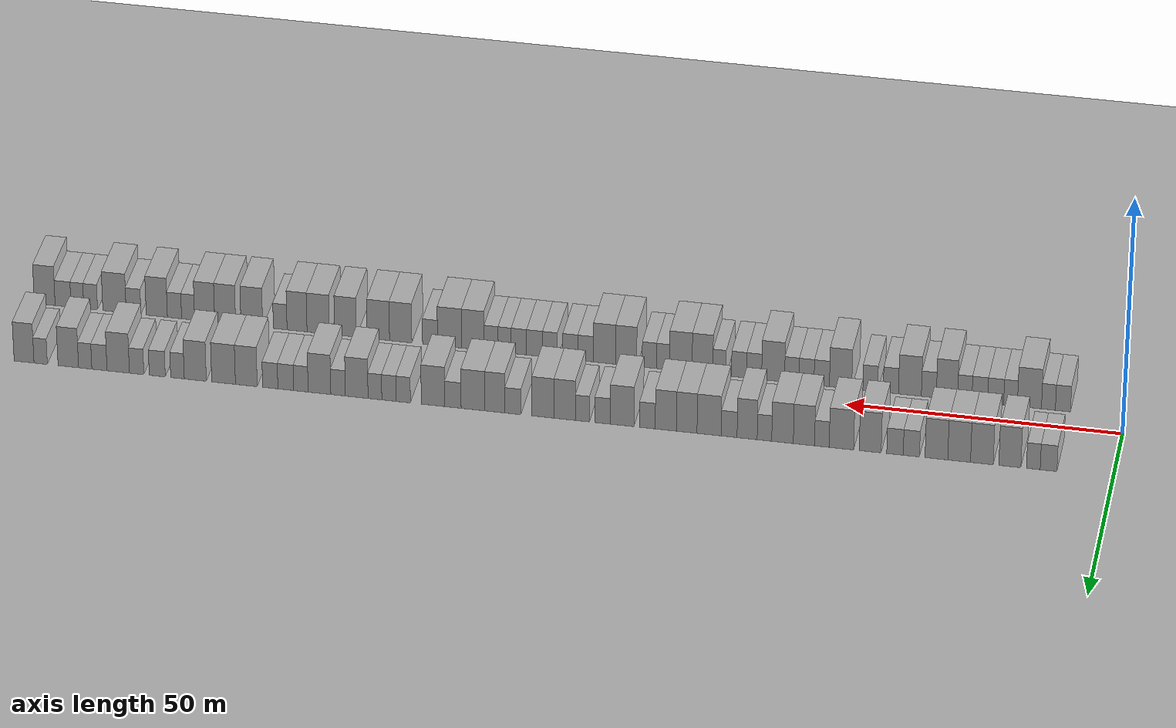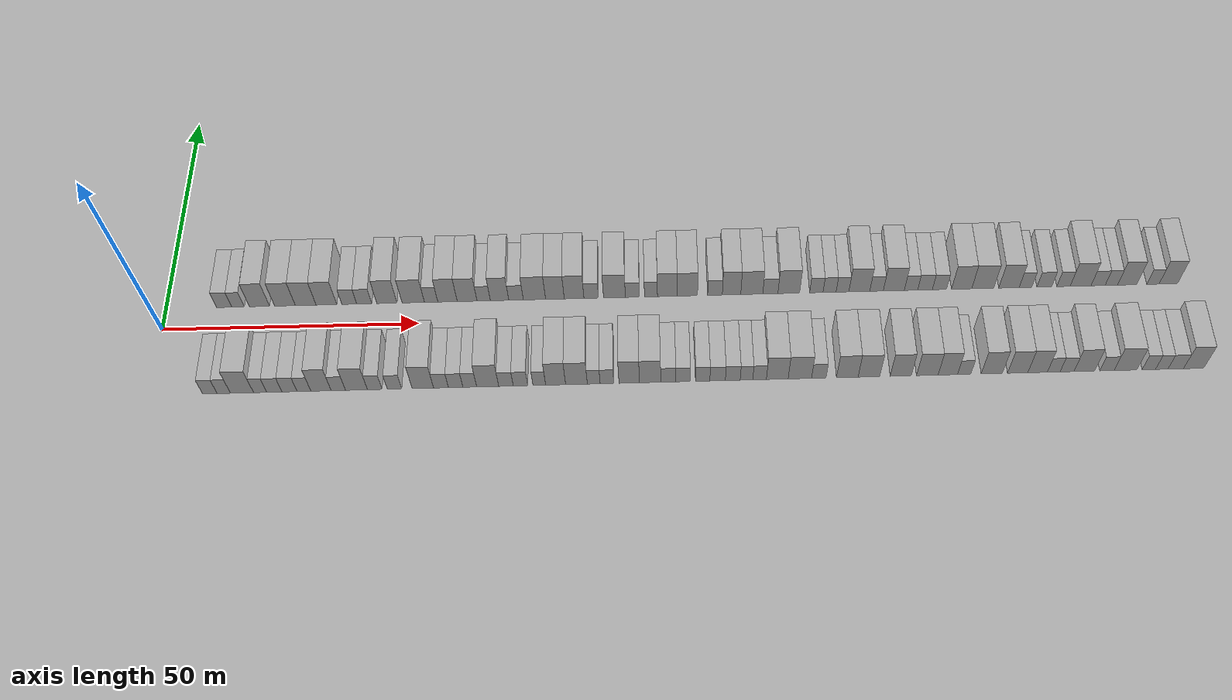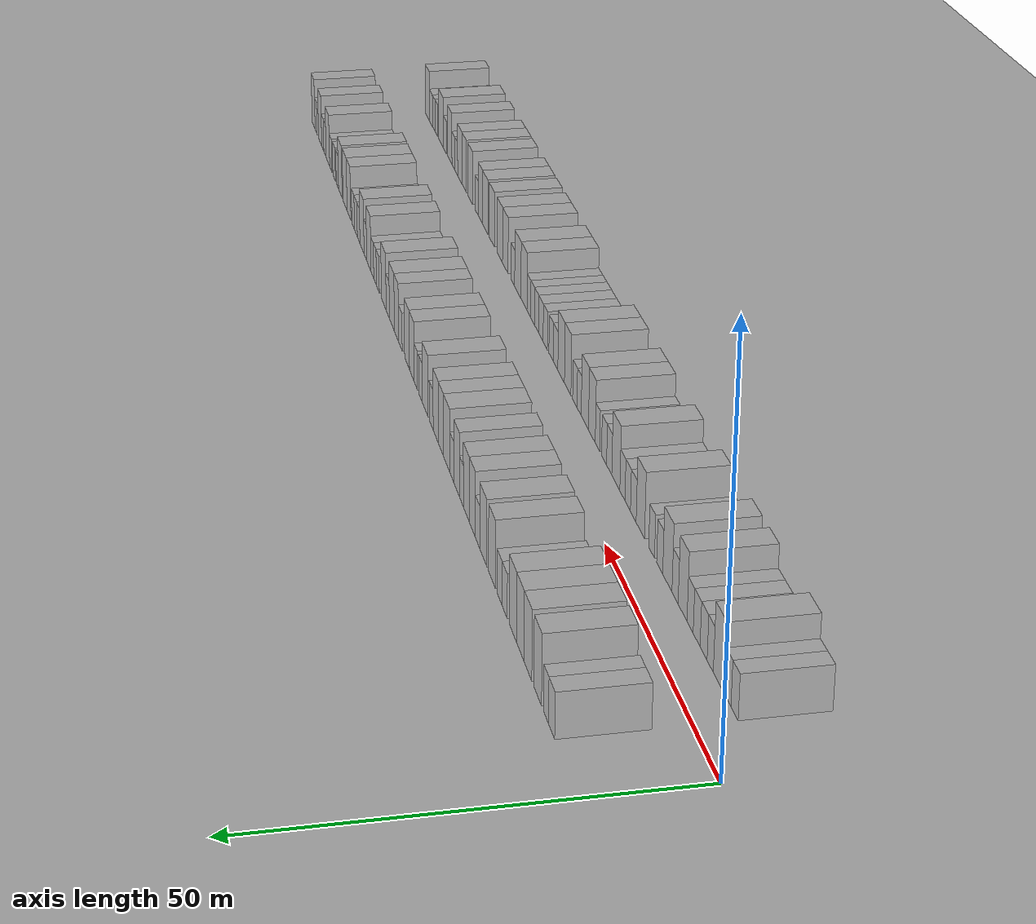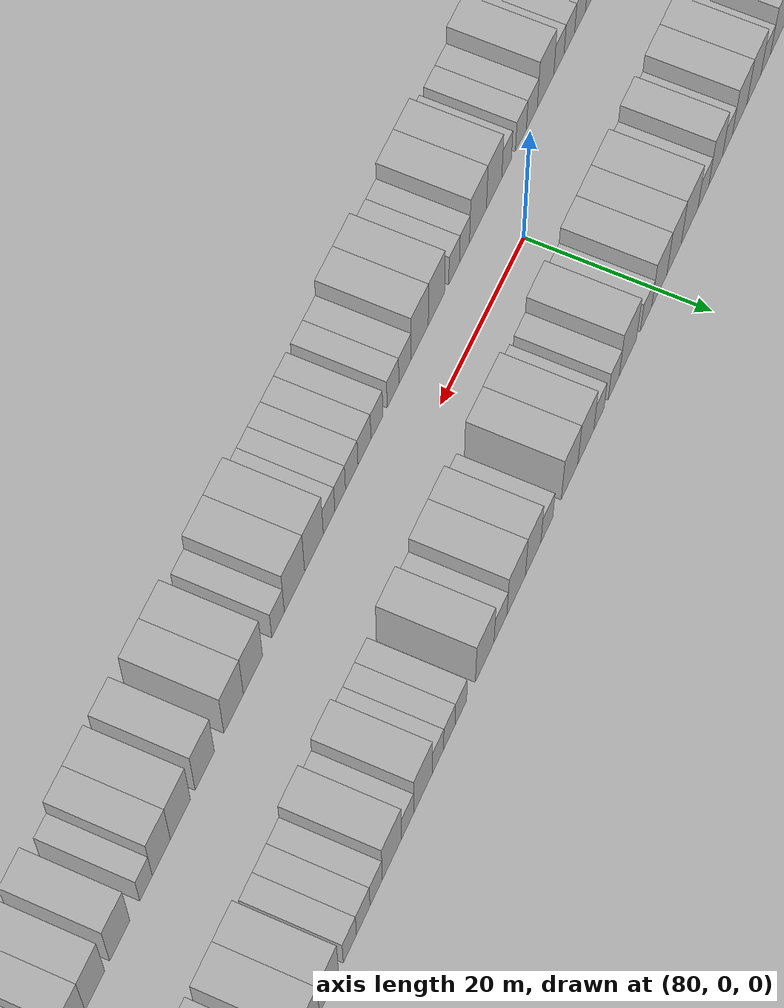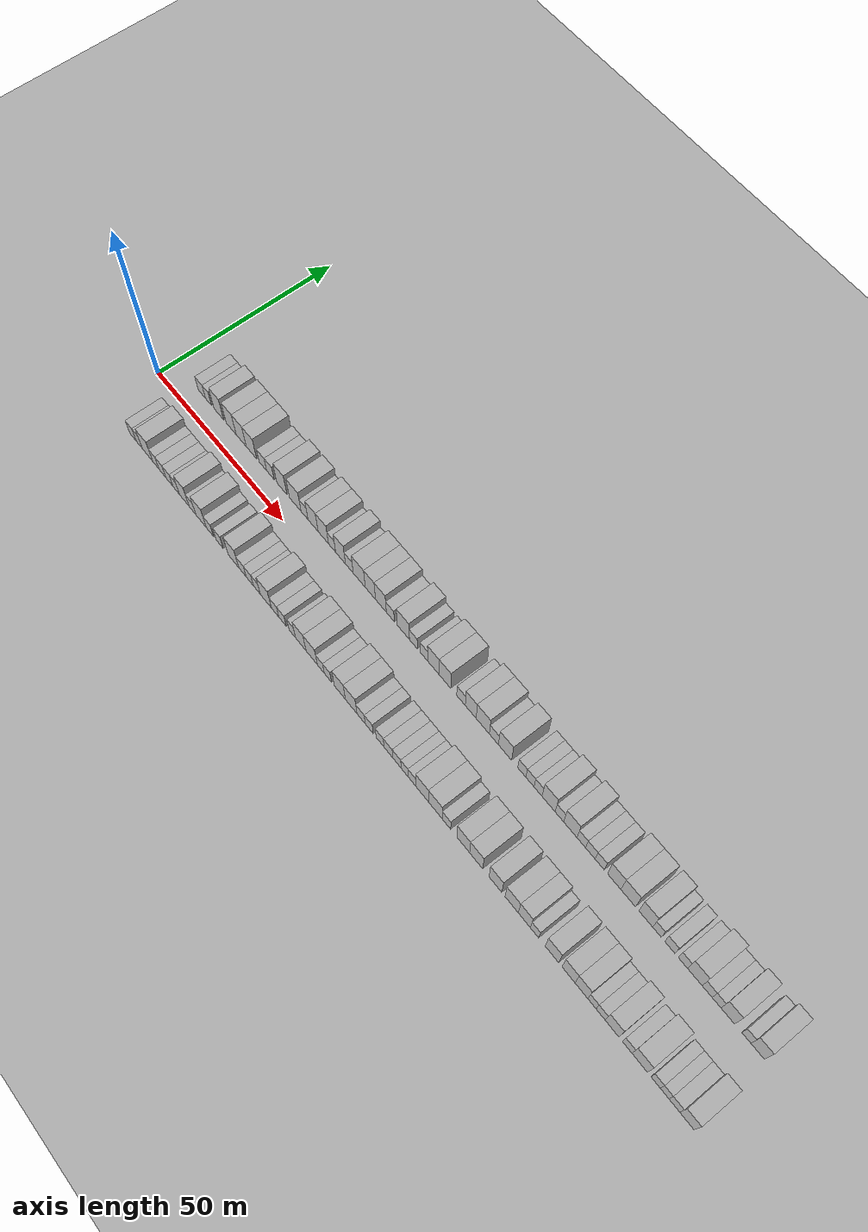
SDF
<?xml version="1.0" encoding="utf-8"?>

<sdf version="1.6">

   <world name="default">

      <gui fullscreen="0">

         <camera name="user_camera">

            <pose>-15 0 4.57585 0 0 0</pose>

            <view_controller>orbit</view_controller>

         </camera>

      </gui>

      <scene>

         <sky>

           <clouds>

             <speed>12</speed>

           </clouds>

         </sky>

         <ambient>0.4 0.4 0.4 1</ambient>

         <background>0.7 0.7 0.7 1</background>

         <shadows>1</shadows>

      </scene>

      <gravity>0 0 -9.8066</gravity>

      <magnetic_field>6e-06 2.3e-05 -4.2e-05</magnetic_field>

      <physics default="0" name="default_physics" type="ode">

         <ode>

            <solver>

               <type>quick</type>

               <iters>10</iters>

               <sor>1.0</sor>

               <use_dynamic_moi_rescaling>0</use_dynamic_moi_rescaling>

            </solver>

            <constraints>

               <cfm>0</cfm>

               <erp>0.2</erp>

               <contact_max_correcting_vel>100</contact_max_correcting_vel>

               <contact_surface_layer>0.001</contact_surface_layer>

            </constraints>

         </ode>

         <max_step_size>0.004</max_step_size>

         <real_time_factor>1</real_time_factor>

         <real_time_update_rate>250</real_time_update_rate>

      </physics>

      <light name="sun" type="directional">

         <cast_shadows>1</cast_shadows>

         <pose>0 0 10 0 0 0</pose>

         <diffuse>0.8 0.8 0.8 1</diffuse>

         <specular>0.2 0.2 0.2 1</specular>

         <attenuation>

            <range>1000</range>

            <constant>0.9</constant>

            <linear>0.01</linear>

            <quadratic>0.001</quadratic>

         </attenuation>

         <direction>-0.5 0.1 -0.9</direction>

      </light>

      <include>

         <name>ground_plane_1</name>

         <uri>model://HANNAS_ground_plane</uri>

         <pose>0 0 0  0 0 0</pose>

      </include>

      <include>

         <name>ground_plane_2</name>

         <uri>model://HANNAS_ground_plane</uri>

         <pose>100 0 0  0 0 0</pose>

      </include>

      <model name="building_1">

         <static>1</static>

         <pose frame="">11.4937 9.5000 0 0.000000 0.000000 1.570796</pose>

         <link name="link">

            <pose frame="">0 0 3.00 0 0 0</pose>

            <collision name="collision">

               <geometry>

                  <box>

                     <size>10.0000 2.9875 6.0000</size>

                  </box>

               </geometry>

               <max_contacts>10</max_contacts>

               <surface>

                  <contact>

                     <ode/>

                  </contact>

                  <bounce/>

                  <friction>

                     <torsional>

                        <ode/>

                     </torsional>

                     <ode/>

                  </friction>

               </surface>

            </collision>

            <visual name="visual">

               <cast_shadows>0</cast_shadows>

               <geometry>

                  <box>

                     <size>10.0000 2.9875 6.0000</size>

                  </box>

               </geometry>

               <material>

                  <script>

                     <uri>model://HANNAS_wall/materials/scripts</uri>

                     <uri>model://HANNAS_wall/materials/textures</uri>

                     <name>vrc/HANNAS_wall</name>

                  </script>

               </material>

            </visual>

            <self_collide>0</self_collide>

            <enable_wind>0</enable_wind>

            <kinematic>0</kinematic>

         </link>

      </model>

      <model name="building_2">

         <static>1</static>

         <pose frame="">14.2155 9.5000 0 0.000000 0.000000 1.570796</pose>

         <link name="link">

            <pose frame="">0 0 3.00 0 0 0</pose>

            <collision name="collision">

               <geometry>

                  <box>

                     <size>10.0000 2.4561 6.0000</size>

                  </box>

               </geometry>

               <max_contacts>10</max_contacts>

               <surface>

                  <contact>

                     <ode/>

                  </contact>

                  <bounce/>

                  <friction>

                     <torsional>

                        <ode/>

                     </torsional>

                     <ode/>

                  </friction>

               </surface>

            </collision>

            <visual name="visual">

               <cast_shadows>0</cast_shadows>

               <geometry>

                  <box>

                     <size>10.0000 2.4561 6.0000</size>

                  </box>

               </geometry>

               <material>

                  <script>

                     <uri>model://HANNAS_wall/materials/scripts</uri>

                     <uri>model://HANNAS_wall/materials/textures</uri>

                     <name>vrc/HANNAS_wall</name>

                  </script>

               </material>

            </visual>

            <self_collide>0</self_collide>

            <enable_wind>0</enable_wind>

            <kinematic>0</kinematic>

         </link>

      </model>

      <model name="building_3">

         <static>1</static>

         <pose frame="">18.4167 9.5000 0 0.000000 0.000000 1.570796</pose>

         <link name="link">

            <pose frame="">0 0 4.50 0 0 0</pose>

            <collision name="collision">

               <geometry>

                  <box>

                     <size>10.0000 3.9462 9.0000</size>

                  </box>

               </geometry>

               <max_contacts>10</max_contacts>

               <surface>

                  <contact>

                     <ode/>

                  </contact>

                  <bounce/>

                  <friction>

                     <torsional>

                        <ode/>

                     </torsional>

                     <ode/>

                  </friction>

               </surface>

            </collision>

            <visual name="visual">

               <cast_shadows>0</cast_shadows>

               <geometry>

                  <box>

                     <size>10.0000 3.9462 9.0000</size>

                  </box>

               </geometry>

               <material>

                  <script>

                     <uri>model://HANNAS_wall/materials/scripts</uri>

                     <uri>model://HANNAS_wall/materials/textures</uri>

                     <name>vrc/HANNAS_wall</name>

                  </script>

               </material>

            </visual>

            <self_collide>0</self_collide>

            <enable_wind>0</enable_wind>

            <kinematic>0</kinematic>

         </link>

      </model>

      <model name="building_4">

         <static>1</static>

         <pose frame="">23.4204 9.5000 0 0.000000 0.000000 1.570796</pose>

         <link name="link">

            <pose frame="">0 0 4.50 0 0 0</pose>

            <collision name="collision">

               <geometry>

                  <box>

                     <size>10.0000 4.0612 9.0000</size>

                  </box>

               </geometry>

               <max_contacts>10</max_contacts>

               <surface>

                  <contact>

                     <ode/>

                  </contact>

                  <bounce/>

                  <friction>

                     <torsional>

                        <ode/>

                     </torsional>

                     <ode/>

                  </friction>

               </surface>

            </collision>

            <visual name="visual">

               <cast_shadows>0</cast_shadows>

               <geometry>

                  <box>

                     <size>10.0000 4.0612 9.0000</size>

                  </box>

               </geometry>

               <material>

                  <script>

                     <uri>model://HANNAS_wall/materials/scripts</uri>

                     <uri>model://HANNAS_wall/materials/textures</uri>

                     <name>vrc/HANNAS_wall</name>

                  </script>

               </material>

            </visual>

            <self_collide>0</self_collide>

            <enable_wind>0</enable_wind>

            <kinematic>0</kinematic>

         </link>

      </model>

      <model name="building_5">

         <static>1</static>

         <pose frame="">27.4896 9.5000 0 0.000000 0.000000 1.570796</pose>

         <link name="link">

            <pose frame="">0 0 4.50 0 0 0</pose>

            <collision name="collision">

               <geometry>

                  <box>

                     <size>10.0000 4.0774 9.0000</size>

                  </box>

               </geometry>

               <max_contacts>10</max_contacts>

               <surface>

                  <contact>

                     <ode/>

                  </contact>

                  <bounce/>

                  <friction>

                     <torsional>

                        <ode/>

                     </torsional>

                     <ode/>

                  </friction>

               </surface>

            </collision>

            <visual name="visual">

               <cast_shadows>0</cast_shadows>

               <geometry>

                  <box>

                     <size>10.0000 4.0774 9.0000</size>

                  </box>

               </geometry>

               <material>

                  <script>

                     <uri>model://HANNAS_wall/materials/scripts</uri>

                     <uri>model://HANNAS_wall/materials/textures</uri>

                     <name>vrc/HANNAS_wall</name>

                  </script>

               </material>

            </visual>

            <self_collide>0</self_collide>

            <enable_wind>0</enable_wind>

            <kinematic>0</kinematic>

         </link>

      </model>

      <model name="building_6">

         <static>1</static>

         <pose frame="">31.5653 9.5000 0 0.000000 0.000000 1.570796</pose>

         <link name="link">

            <pose frame="">0 0 4.50 0 0 0</pose>

            <collision name="collision">

               <geometry>

                  <box>

                     <size>10.0000 4.0740 9.0000</size>

                  </box>

               </geometry>

               <max_contacts>10</max_contacts>

               <surface>

                  <contact>

                     <ode/>

                  </contact>

                  <bounce/>

                  <friction>

                     <torsional>

                        <ode/>

                     </torsional>

                     <ode/>

                  </friction>

               </surface>

            </collision>

            <visual name="visual">

               <cast_shadows>0</cast_shadows>

               <geometry>

                  <box>

                     <size>10.0000 4.0740 9.0000</size>

                  </box>

               </geometry>

               <material>

                  <script>

                     <uri>model://HANNAS_wall/materials/scripts</uri>

                     <uri>model://HANNAS_wall/materials/textures</uri>

                     <name>vrc/HANNAS_wall</name>

                  </script>

               </material>

            </visual>

            <self_collide>0</self_collide>

            <enable_wind>0</enable_wind>

            <kinematic>0</kinematic>

         </link>

      </model>

      <model name="building_7">

         <static>1</static>

         <pose frame="">36.0594 9.5000 0 0.000000 0.000000 1.570796</pose>

         <link name="link">

            <pose frame="">0 0 3.00 0 0 0</pose>

            <collision name="collision">

               <geometry>

                  <box>

                     <size>10.0000 2.9140 6.0000</size>

                  </box>

               </geometry>

               <max_contacts>10</max_contacts>

               <surface>

                  <contact>

                     <ode/>

                  </contact>

                  <bounce/>

                  <friction>

                     <torsional>

                        <ode/>

                     </torsional>

                     <ode/>

                  </friction>

               </surface>

            </collision>

            <visual name="visual">

               <cast_shadows>0</cast_shadows>

               <geometry>

                  <box>

                     <size>10.0000 2.9140 6.0000</size>

                  </box>

               </geometry>

               <material>

                  <script>

                     <uri>model://HANNAS_wall/materials/scripts</uri>

                     <uri>model://HANNAS_wall/materials/textures</uri>

                     <name>vrc/HANNAS_wall</name>

                  </script>

               </material>

            </visual>

            <self_collide>0</self_collide>

            <enable_wind>0</enable_wind>

            <kinematic>0</kinematic>

         </link>

      </model>

      <model name="building_8">

         <static>1</static>

         <pose frame="">38.9993 9.5000 0 0.000000 0.000000 1.570796</pose>

         <link name="link">

            <pose frame="">0 0 3.00 0 0 0</pose>

            <collision name="collision">

               <geometry>

                  <box>

                     <size>10.0000 2.9658 6.0000</size>

                  </box>

               </geometry>

               <max_contacts>10</max_contacts>

               <surface>

                  <contact>

                     <ode/>

                  </contact>

                  <bounce/>

                  <friction>

                     <torsional>

                        <ode/>

                     </torsional>

                     <ode/>

                  </friction>

               </surface>

            </collision>

            <visual name="visual">

               <cast_shadows>0</cast_shadows>

               <geometry>

                  <box>

                     <size>10.0000 2.9658 6.0000</size>

                  </box>

               </geometry>

               <material>

                  <script>

                     <uri>model://HANNAS_wall/materials/scripts</uri>

                     <uri>model://HANNAS_wall/materials/textures</uri>

                     <name>vrc/HANNAS_wall</name>

                  </script>

               </material>

            </visual>

            <self_collide>0</self_collide>

            <enable_wind>0</enable_wind>

            <kinematic>0</kinematic>

         </link>

      </model>

      <model name="building_9">

         <static>1</static>

         <pose frame="">43.4593 9.5000 0 0.000000 0.000000 1.570796</pose>

         <link name="link">

            <pose frame="">0 0 4.50 0 0 0</pose>

            <collision name="collision">

               <geometry>

                  <box>

                     <size>10.0000 3.9543 9.0000</size>

                  </box>

               </geometry>

               <max_contacts>10</max_contacts>

               <surface>

                  <contact>

                     <ode/>

                  </contact>

                  <bounce/>

                  <friction>

                     <torsional>

                        <ode/>

                     </torsional>

                     <ode/>

                  </friction>

               </surface>

            </collision>

            <visual name="visual">

               <cast_shadows>0</cast_shadows>

               <geometry>

                  <box>

                     <size>10.0000 3.9543 9.0000</size>

                  </box>

               </geometry>

               <material>

                  <script>

                     <uri>model://HANNAS_wall/materials/scripts</uri>

                     <uri>model://HANNAS_wall/materials/textures</uri>

                     <name>vrc/HANNAS_wall</name>

                  </script>

               </material>

            </visual>

            <self_collide>0</self_collide>

            <enable_wind>0</enable_wind>

            <kinematic>0</kinematic>

         </link>

      </model>

      <model name="building_10">

         <static>1</static>

         <pose frame="">48.6359 9.5000 0 0.000000 0.000000 1.570796</pose>

         <link name="link">

            <pose frame="">0 0 4.50 0 0 0</pose>

            <collision name="collision">

               <geometry>

                  <box>

                     <size>10.0000 4.3989 9.0000</size>

                  </box>

               </geometry>

               <max_contacts>10</max_contacts>

               <surface>

                  <contact>

                     <ode/>

                  </contact>

                  <bounce/>

                  <friction>

                     <torsional>

                        <ode/>

                     </torsional>

                     <ode/>

                  </friction>

               </surface>

            </collision>

            <visual name="visual">

               <cast_shadows>0</cast_shadows>

               <geometry>

                  <box>

                     <size>10.0000 4.3989 9.0000</size>

                  </box>

               </geometry>

               <material>

                  <script>

                     <uri>model://HANNAS_wall/materials/scripts</uri>

                     <uri>model://HANNAS_wall/materials/textures</uri>

                     <name>vrc/HANNAS_wall</name>

                  </script>

               </material>

            </visual>

            <self_collide>0</self_collide>

            <enable_wind>0</enable_wind>

            <kinematic>0</kinematic>

         </link>

      </model>

      <model name="building_11">

         <static>1</static>

         <pose frame="">52.1533 9.5000 0 0.000000 0.000000 1.570796</pose>

         <link name="link">

            <pose frame="">0 0 3.00 0 0 0</pose>

            <collision name="collision">

               <geometry>

                  <box>

                     <size>10.0000 2.6358 6.0000</size>

                  </box>

               </geometry>

               <max_contacts>10</max_contacts>

               <surface>

                  <contact>

                     <ode/>

                  </contact>

                  <bounce/>

                  <friction>

                     <torsional>

                        <ode/>

                     </torsional>

                     <ode/>

                  </friction>

               </surface>

            </collision>

            <visual name="visual">

               <cast_shadows>0</cast_shadows>

               <geometry>

                  <box>

                     <size>10.0000 2.6358 6.0000</size>

                  </box>

               </geometry>

               <material>

                  <script>

                     <uri>model://HANNAS_wall/materials/scripts</uri>

                     <uri>model://HANNAS_wall/materials/textures</uri>

                     <name>vrc/HANNAS_wall</name>

                  </script>

               </material>

            </visual>

            <self_collide>0</self_collide>

            <enable_wind>0</enable_wind>

            <kinematic>0</kinematic>

         </link>

      </model>

      <model name="building_12">

         <static>1</static>

         <pose frame="">55.3849 9.5000 0 0.000000 0.000000 1.570796</pose>

         <link name="link">

            <pose frame="">0 0 4.50 0 0 0</pose>

            <collision name="collision">

               <geometry>

                  <box>

                     <size>10.0000 3.8273 9.0000</size>

                  </box>

               </geometry>

               <max_contacts>10</max_contacts>

               <surface>

                  <contact>

                     <ode/>

                  </contact>

                  <bounce/>

                  <friction>

                     <torsional>

                        <ode/>

                     </torsional>

                     <ode/>

                  </friction>

               </surface>

            </collision>

            <visual name="visual">

               <cast_shadows>0</cast_shadows>

               <geometry>

                  <box>

                     <size>10.0000 3.8273 9.0000</size>

                  </box>

               </geometry>

               <material>

                  <script>

                     <uri>model://HANNAS_wall/materials/scripts</uri>

                     <uri>model://HANNAS_wall/materials/textures</uri>

                     <name>vrc/HANNAS_wall</name>

                  </script>

               </material>

            </visual>

            <self_collide>0</self_collide>

            <enable_wind>0</enable_wind>

            <kinematic>0</kinematic>

         </link>

      </model>

      <model name="building_13">

         <static>1</static>

         <pose frame="">59.2486 9.5000 0 0.000000 0.000000 1.570796</pose>

         <link name="link">

            <pose frame="">0 0 4.50 0 0 0</pose>

            <collision name="collision">

               <geometry>

                  <box>

                     <size>10.0000 3.9002 9.0000</size>

                  </box>

               </geometry>

               <max_contacts>10</max_contacts>

               <surface>

                  <contact>

                     <ode/>

                  </contact>

                  <bounce/>

                  <friction>

                     <torsional>

                        <ode/>

                     </torsional>

                     <ode/>

                  </friction>

               </surface>

            </collision>

            <visual name="visual">

               <cast_shadows>0</cast_shadows>

               <geometry>

                  <box>

                     <size>10.0000 3.9002 9.0000</size>

                  </box>

               </geometry>

               <material>

                  <script>

                     <uri>model://HANNAS_wall/materials/scripts</uri>

                     <uri>model://HANNAS_wall/materials/textures</uri>

                     <name>vrc/HANNAS_wall</name>

                  </script>

               </material>

            </visual>

            <self_collide>0</self_collide>

            <enable_wind>0</enable_wind>

            <kinematic>0</kinematic>

         </link>

      </model>

      <model name="building_14">

         <static>1</static>

         <pose frame="">62.5120 9.5000 0 0.000000 0.000000 1.570796</pose>

         <link name="link">

            <pose frame="">0 0 3.00 0 0 0</pose>

            <collision name="collision">

               <geometry>

                  <box>

                     <size>10.0000 2.6267 6.0000</size>

                  </box>

               </geometry>

               <max_contacts>10</max_contacts>

               <surface>

                  <contact>

                     <ode/>

                  </contact>

                  <bounce/>

                  <friction>

                     <torsional>

                        <ode/>

                     </torsional>

                     <ode/>

                  </friction>

               </surface>

            </collision>

            <visual name="visual">

               <cast_shadows>0</cast_shadows>

               <geometry>

                  <box>

                     <size>10.0000 2.6267 6.0000</size>

                  </box>

               </geometry>

               <material>

                  <script>

                     <uri>model://HANNAS_wall/materials/scripts</uri>

                     <uri>model://HANNAS_wall/materials/textures</uri>

                     <name>vrc/HANNAS_wall</name>

                  </script>

               </material>

            </visual>

            <self_collide>0</self_collide>

            <enable_wind>0</enable_wind>

            <kinematic>0</kinematic>

         </link>

      </model>

      <model name="building_15">

         <static>1</static>

         <pose frame="">65.6415 9.5000 0 0.000000 0.000000 1.570796</pose>

         <link name="link">

            <pose frame="">0 0 4.50 0 0 0</pose>

            <collision name="collision">

               <geometry>

                  <box>

                     <size>10.0000 3.6323 9.0000</size>

                  </box>

               </geometry>

               <max_contacts>10</max_contacts>

               <surface>

                  <contact>

                     <ode/>

                  </contact>

                  <bounce/>

                  <friction>

                     <torsional>

                        <ode/>

                     </torsional>

                     <ode/>

                  </friction>

               </surface>

            </collision>

            <visual name="visual">

               <cast_shadows>0</cast_shadows>

               <geometry>

                  <box>

                     <size>10.0000 3.6323 9.0000</size>

                  </box>

               </geometry>

               <material>

                  <script>

                     <uri>model://HANNAS_wall/materials/scripts</uri>

                     <uri>model://HANNAS_wall/materials/textures</uri>

                     <name>vrc/HANNAS_wall</name>

                  </script>

               </material>

            </visual>

            <self_collide>0</self_collide>

            <enable_wind>0</enable_wind>

            <kinematic>0</kinematic>

         </link>

      </model>

      <model name="building_16">

         <static>1</static>

         <pose frame="">68.8954 9.5000 0 0.000000 0.000000 1.570796</pose>

         <link name="link">

            <pose frame="">0 0 3.00 0 0 0</pose>

            <collision name="collision">

               <geometry>

                  <box>

                     <size>10.0000 2.8755 6.0000</size>

                  </box>

               </geometry>

               <max_contacts>10</max_contacts>

               <surface>

                  <contact>

                     <ode/>

                  </contact>

                  <bounce/>

                  <friction>

                     <torsional>

                        <ode/>

                     </torsional>

                     <ode/>

                  </friction>

               </surface>

            </collision>

            <visual name="visual">

               <cast_shadows>0</cast_shadows>

               <geometry>

                  <box>

                     <size>10.0000 2.8755 6.0000</size>

                  </box>

               </geometry>

               <material>

                  <script>

                     <uri>model://HANNAS_wall/materials/scripts</uri>

                     <uri>model://HANNAS_wall/materials/textures</uri>

                     <name>vrc/HANNAS_wall</name>

                  </script>

               </material>

            </visual>

            <self_collide>0</self_collide>

            <enable_wind>0</enable_wind>

            <kinematic>0</kinematic>

         </link>

      </model>

      <model name="building_17">

         <static>1</static>

         <pose frame="">72.5236 9.5000 0 0.000000 0.000000 1.570796</pose>

         <link name="link">

            <pose frame="">0 0 4.50 0 0 0</pose>

            <collision name="collision">

               <geometry>

                  <box>

                     <size>10.0000 4.3809 9.0000</size>

                  </box>

               </geometry>

               <max_contacts>10</max_contacts>

               <surface>

                  <contact>

                     <ode/>

                  </contact>

                  <bounce/>

                  <friction>

                     <torsional>

                        <ode/>

                     </torsional>

                     <ode/>

                  </friction>

               </surface>

            </collision>

            <visual name="visual">

               <cast_shadows>0</cast_shadows>

               <geometry>

                  <box>

                     <size>10.0000 4.3809 9.0000</size>

                  </box>

               </geometry>

               <material>

                  <script>

                     <uri>model://HANNAS_wall/materials/scripts</uri>

                     <uri>model://HANNAS_wall/materials/textures</uri>

                     <name>vrc/HANNAS_wall</name>

                  </script>

               </material>

            </visual>

            <self_collide>0</self_collide>

            <enable_wind>0</enable_wind>

            <kinematic>0</kinematic>

         </link>

      </model>

      <model name="building_18">

         <static>1</static>

         <pose frame="">76.5592 9.5000 0 0.000000 0.000000 1.570796</pose>

         <link name="link">

            <pose frame="">0 0 4.50 0 0 0</pose>

            <collision name="collision">

               <geometry>

                  <box>

                     <size>10.0000 3.6902 9.0000</size>

                  </box>

               </geometry>

               <max_contacts>10</max_contacts>

               <surface>

                  <contact>

                     <ode/>

                  </contact>

                  <bounce/>

                  <friction>

                     <torsional>

                        <ode/>

                     </torsional>

                     <ode/>

                  </friction>

               </surface>

            </collision>

            <visual name="visual">

               <cast_shadows>0</cast_shadows>

               <geometry>

                  <box>

                     <size>10.0000 3.6902 9.0000</size>

                  </box>

               </geometry>

               <material>

                  <script>

                     <uri>model://HANNAS_wall/materials/scripts</uri>

                     <uri>model://HANNAS_wall/materials/textures</uri>

                     <name>vrc/HANNAS_wall</name>

                  </script>

               </material>

            </visual>

            <self_collide>0</self_collide>

            <enable_wind>0</enable_wind>

            <kinematic>0</kinematic>

         </link>

      </model>

      <model name="building_19">

         <static>1</static>

         <pose frame="">80.3442 9.5000 0 0.000000 0.000000 1.570796</pose>

         <link name="link">

            <pose frame="">0 0 4.50 0 0 0</pose>

            <collision name="collision">

               <geometry>

                  <box>

                     <size>10.0000 3.8799 9.0000</size>

                  </box>

               </geometry>

               <max_contacts>10</max_contacts>

               <surface>

                  <contact>

                     <ode/>

                  </contact>

                  <bounce/>

                  <friction>

                     <torsional>

                        <ode/>

                     </torsional>

                     <ode/>

                  </friction>

               </surface>

            </collision>

            <visual name="visual">

               <cast_shadows>0</cast_shadows>

               <geometry>

                  <box>

                     <size>10.0000 3.8799 9.0000</size>

                  </box>

               </geometry>

               <material>

                  <script>

                     <uri>model://HANNAS_wall/materials/scripts</uri>

                     <uri>model://HANNAS_wall/materials/textures</uri>

                     <name>vrc/HANNAS_wall</name>

                  </script>

               </material>

            </visual>

            <self_collide>0</self_collide>

            <enable_wind>0</enable_wind>

            <kinematic>0</kinematic>

         </link>

      </model>

      <model name="building_20">

         <static>1</static>

         <pose frame="">83.7181 9.5000 0 0.000000 0.000000 1.570796</pose>

         <link name="link">

            <pose frame="">0 0 3.00 0 0 0</pose>

            <collision name="collision">

               <geometry>

                  <box>

                     <size>10.0000 2.8679 6.0000</size>

                  </box>

               </geometry>

               <max_contacts>10</max_contacts>

               <surface>

                  <contact>

                     <ode/>

                  </contact>

                  <bounce/>

                  <friction>

                     <torsional>

                        <ode/>

                     </torsional>

                     <ode/>

                  </friction>

               </surface>

            </collision>

            <visual name="visual">

               <cast_shadows>0</cast_shadows>

               <geometry>

                  <box>

                     <size>10.0000 2.8679 6.0000</size>

                  </box>

               </geometry>

               <material>

                  <script>

                     <uri>model://HANNAS_wall/materials/scripts</uri>

                     <uri>model://HANNAS_wall/materials/textures</uri>

                     <name>vrc/HANNAS_wall</name>

                  </script>

               </material>

            </visual>

            <self_collide>0</self_collide>

            <enable_wind>0</enable_wind>

            <kinematic>0</kinematic>

         </link>

      </model>

      <model name="building_21">

         <static>1</static>

         <pose frame="">88.3135 9.5000 0 0.000000 0.000000 1.570796</pose>

         <link name="link">

            <pose frame="">0 0 4.50 0 0 0</pose>

            <collision name="collision">

               <geometry>

                  <box>

                     <size>10.0000 4.3228 9.0000</size>

                  </box>

               </geometry>

               <max_contacts>10</max_contacts>

               <surface>

                  <contact>

                     <ode/>

                  </contact>

                  <bounce/>

                  <friction>

                     <torsional>

                        <ode/>

                     </torsional>

                     <ode/>

                  </friction>

               </surface>

            </collision>

            <visual name="visual">

               <cast_shadows>0</cast_shadows>

               <geometry>

                  <box>

                     <size>10.0000 4.3228 9.0000</size>

                  </box>

               </geometry>

               <material>

                  <script>

                     <uri>model://HANNAS_wall/materials/scripts</uri>

                     <uri>model://HANNAS_wall/materials/textures</uri>

                     <name>vrc/HANNAS_wall</name>

                  </script>

               </material>

            </visual>

            <self_collide>0</self_collide>

            <enable_wind>0</enable_wind>

            <kinematic>0</kinematic>

         </link>

      </model>

      <model name="building_22">

         <static>1</static>

         <pose frame="">91.8621 9.5000 0 0.000000 0.000000 1.570796</pose>

         <link name="link">

            <pose frame="">0 0 3.00 0 0 0</pose>

            <collision name="collision">

               <geometry>

                  <box>

                     <size>10.0000 2.7743 6.0000</size>

                  </box>

               </geometry>

               <max_contacts>10</max_contacts>

               <surface>

                  <contact>

                     <ode/>

                  </contact>

                  <bounce/>

                  <friction>

                     <torsional>

                        <ode/>

                     </torsional>

                     <ode/>

                  </friction>

               </surface>

            </collision>

            <visual name="visual">

               <cast_shadows>0</cast_shadows>

               <geometry>

                  <box>

                     <size>10.0000 2.7743 6.0000</size>

                  </box>

               </geometry>

               <material>

                  <script>

                     <uri>model://HANNAS_wall/materials/scripts</uri>

                     <uri>model://HANNAS_wall/materials/textures</uri>

                     <name>vrc/HANNAS_wall</name>

                  </script>

               </material>

            </visual>

            <self_collide>0</self_collide>

            <enable_wind>0</enable_wind>

            <kinematic>0</kinematic>

         </link>

      </model>

      <model name="building_23">

         <static>1</static>

         <pose frame="">95.5293 9.5000 0 0.000000 0.000000 1.570796</pose>

         <link name="link">

            <pose frame="">0 0 3.00 0 0 0</pose>

            <collision name="collision">

               <geometry>

                  <box>

                     <size>10.0000 2.5601 6.0000</size>

                  </box>

               </geometry>

               <max_contacts>10</max_contacts>

               <surface>

                  <contact>

                     <ode/>

                  </contact>

                  <bounce/>

                  <friction>

                     <torsional>

                        <ode/>

                     </torsional>

                     <ode/>

                  </friction>

               </surface>

            </collision>

            <visual name="visual">

               <cast_shadows>0</cast_shadows>

               <geometry>

                  <box>

                     <size>10.0000 2.5601 6.0000</size>

                  </box>

               </geometry>

               <material>

                  <script>

                     <uri>model://HANNAS_wall/materials/scripts</uri>

                     <uri>model://HANNAS_wall/materials/textures</uri>

                     <name>vrc/HANNAS_wall</name>

                  </script>

               </material>

            </visual>

            <self_collide>0</self_collide>

            <enable_wind>0</enable_wind>

            <kinematic>0</kinematic>

         </link>

      </model>

      <model name="building_24">

         <static>1</static>

         <pose frame="">98.7638 9.5000 0 0.000000 0.000000 1.570796</pose>

         <link name="link">

            <pose frame="">0 0 4.50 0 0 0</pose>

            <collision name="collision">

               <geometry>

                  <box>

                     <size>10.0000 3.9090 9.0000</size>

                  </box>

               </geometry>

               <max_contacts>10</max_contacts>

               <surface>

                  <contact>

                     <ode/>

                  </contact>

                  <bounce/>

                  <friction>

                     <torsional>

                        <ode/>

                     </torsional>

                     <ode/>

                  </friction>

               </surface>

            </collision>

            <visual name="visual">

               <cast_shadows>0</cast_shadows>

               <geometry>

                  <box>

                     <size>10.0000 3.9090 9.0000</size>

                  </box>

               </geometry>

               <material>

                  <script>

                     <uri>model://HANNAS_wall/materials/scripts</uri>

                     <uri>model://HANNAS_wall/materials/textures</uri>

                     <name>vrc/HANNAS_wall</name>

                  </script>

               </material>

            </visual>

            <self_collide>0</self_collide>

            <enable_wind>0</enable_wind>

            <kinematic>0</kinematic>

         </link>

      </model>

      <model name="building_25">

         <static>1</static>

         <pose frame="">102.7310 9.5000 0 0.000000 0.000000 1.570796</pose>

         <link name="link">

            <pose frame="">0 0 4.50 0 0 0</pose>

            <collision name="collision">

               <geometry>

                  <box>

                     <size>10.0000 4.0255 9.0000</size>

                  </box>

               </geometry>

               <max_contacts>10</max_contacts>

               <surface>

                  <contact>

                     <ode/>

                  </contact>

                  <bounce/>

                  <friction>

                     <torsional>

                        <ode/>

                     </torsional>

                     <ode/>

                  </friction>

               </surface>

            </collision>

            <visual name="visual">

               <cast_shadows>0</cast_shadows>

               <geometry>

                  <box>

                     <size>10.0000 4.0255 9.0000</size>

                  </box>

               </geometry>

               <material>

                  <script>

                     <uri>model://HANNAS_wall/materials/scripts</uri>

                     <uri>model://HANNAS_wall/materials/textures</uri>

                     <name>vrc/HANNAS_wall</name>

                  </script>

               </material>

            </visual>

            <self_collide>0</self_collide>

            <enable_wind>0</enable_wind>

            <kinematic>0</kinematic>

         </link>

      </model>

      <model name="building_26">

         <static>1</static>

         <pose frame="">108.1972 9.5000 0 0.000000 0.000000 1.570796</pose>

         <link name="link">

            <pose frame="">0 0 3.00 0 0 0</pose>

            <collision name="collision">

               <geometry>

                  <box>

                     <size>10.0000 2.9069 6.0000</size>

                  </box>

               </geometry>

               <max_contacts>10</max_contacts>

               <surface>

                  <contact>

                     <ode/>

                  </contact>

                  <bounce/>

                  <friction>

                     <torsional>

                        <ode/>

                     </torsional>

                     <ode/>

                  </friction>

               </surface>

            </collision>

            <visual name="visual">

               <cast_shadows>0</cast_shadows>

               <geometry>

                  <box>

                     <size>10.0000 2.9069 6.0000</size>

                  </box>

               </geometry>

               <material>

                  <script>

                     <uri>model://HANNAS_wall/materials/scripts</uri>

                     <uri>model://HANNAS_wall/materials/textures</uri>

                     <name>vrc/HANNAS_wall</name>

                  </script>

               </material>

            </visual>

            <self_collide>0</self_collide>

            <enable_wind>0</enable_wind>

            <kinematic>0</kinematic>

         </link>

      </model>

      <model name="building_27">

         <static>1</static>

         <pose frame="">111.4768 9.5000 0 0.000000 0.000000 1.570796</pose>

         <link name="link">

            <pose frame="">0 0 4.50 0 0 0</pose>

            <collision name="collision">

               <geometry>

                  <box>

                     <size>10.0000 3.6522 9.0000</size>

                  </box>

               </geometry>

               <max_contacts>10</max_contacts>

               <surface>

                  <contact>

                     <ode/>

                  </contact>

                  <bounce/>

                  <friction>

                     <torsional>

                        <ode/>

                     </torsional>

                     <ode/>

                  </friction>

               </surface>

            </collision>

            <visual name="visual">

               <cast_shadows>0</cast_shadows>

               <geometry>

                  <box>

                     <size>10.0000 3.6522 9.0000</size>

                  </box>

               </geometry>

               <material>

                  <script>

                     <uri>model://HANNAS_wall/materials/scripts</uri>

                     <uri>model://HANNAS_wall/materials/textures</uri>

                     <name>vrc/HANNAS_wall</name>

                  </script>

               </material>

            </visual>

            <self_collide>0</self_collide>

            <enable_wind>0</enable_wind>

            <kinematic>0</kinematic>

         </link>

      </model>

      <model name="building_28">

         <static>1</static>

         <pose frame="">115.4859 9.5000 0 0.000000 0.000000 1.570796</pose>

         <link name="link">

            <pose frame="">0 0 4.50 0 0 0</pose>

            <collision name="collision">

               <geometry>

                  <box>

                     <size>10.0000 4.3660 9.0000</size>

                  </box>

               </geometry>

               <max_contacts>10</max_contacts>

               <surface>

                  <contact>

                     <ode/>

                  </contact>

                  <bounce/>

                  <friction>

                     <torsional>

                        <ode/>

                     </torsional>

                     <ode/>

                  </friction>

               </surface>

            </collision>

            <visual name="visual">

               <cast_shadows>0</cast_shadows>

               <geometry>

                  <box>

                     <size>10.0000 4.3660 9.0000</size>

                  </box>

               </geometry>

               <material>

                  <script>

                     <uri>model://HANNAS_wall/materials/scripts</uri>

                     <uri>model://HANNAS_wall/materials/textures</uri>

                     <name>vrc/HANNAS_wall</name>

                  </script>

               </material>

            </visual>

            <self_collide>0</self_collide>

            <enable_wind>0</enable_wind>

            <kinematic>0</kinematic>

         </link>

      </model>

      <model name="building_29">

         <static>1</static>

         <pose frame="">119.1669 9.5000 0 0.000000 0.000000 1.570796</pose>

         <link name="link">

            <pose frame="">0 0 3.00 0 0 0</pose>

            <collision name="collision">

               <geometry>

                  <box>

                     <size>10.0000 2.9960 6.0000</size>

                  </box>

               </geometry>

               <max_contacts>10</max_contacts>

               <surface>

                  <contact>

                     <ode/>

                  </contact>

                  <bounce/>

                  <friction>

                     <torsional>

                        <ode/>

                     </torsional>

                     <ode/>

                  </friction>

               </surface>

            </collision>

            <visual name="visual">

               <cast_shadows>0</cast_shadows>

               <geometry>

                  <box>

                     <size>10.0000 2.9960 6.0000</size>

                  </box>

               </geometry>

               <material>

                  <script>

                     <uri>model://HANNAS_wall/materials/scripts</uri>

                     <uri>model://HANNAS_wall/materials/textures</uri>

                     <name>vrc/HANNAS_wall</name>

                  </script>

               </material>

            </visual>

            <self_collide>0</self_collide>

            <enable_wind>0</enable_wind>

            <kinematic>0</kinematic>

         </link>

      </model>

      <model name="building_30">

         <static>1</static>

         <pose frame="">122.8163 9.5000 0 0.000000 0.000000 1.570796</pose>

         <link name="link">

            <pose frame="">0 0 4.50 0 0 0</pose>

            <collision name="collision">

               <geometry>

                  <box>

                     <size>10.0000 4.3029 9.0000</size>

                  </box>

               </geometry>

               <max_contacts>10</max_contacts>

               <surface>

                  <contact>

                     <ode/>

                  </contact>

                  <bounce/>

                  <friction>

                     <torsional>

                        <ode/>

                     </torsional>

                     <ode/>

                  </friction>

               </surface>

            </collision>

            <visual name="visual">

               <cast_shadows>0</cast_shadows>

               <geometry>

                  <box>

                     <size>10.0000 4.3029 9.0000</size>

                  </box>

               </geometry>

               <material>

                  <script>

                     <uri>model://HANNAS_wall/materials/scripts</uri>

                     <uri>model://HANNAS_wall/materials/textures</uri>

                     <name>vrc/HANNAS_wall</name>

                  </script>

               </material>

            </visual>

            <self_collide>0</self_collide>

            <enable_wind>0</enable_wind>

            <kinematic>0</kinematic>

         </link>

      </model>

      <model name="building_31">

         <static>1</static>

         <pose frame="">128.2900 9.5000 0 0.000000 0.000000 1.570796</pose>

         <link name="link">

            <pose frame="">0 0 3.00 0 0 0</pose>

            <collision name="collision">

               <geometry>

                  <box>

                     <size>10.0000 2.6445 6.0000</size>

                  </box>

               </geometry>

               <max_contacts>10</max_contacts>

               <surface>

                  <contact>

                     <ode/>

                  </contact>

                  <bounce/>

                  <friction>

                     <torsional>

                        <ode/>

                     </torsional>

                     <ode/>

                  </friction>

               </surface>

            </collision>

            <visual name="visual">

               <cast_shadows>0</cast_shadows>

               <geometry>

                  <box>

                     <size>10.0000 2.6445 6.0000</size>

                  </box>

               </geometry>

               <material>

                  <script>

                     <uri>model://HANNAS_wall/materials/scripts</uri>

                     <uri>model://HANNAS_wall/materials/textures</uri>

                     <name>vrc/HANNAS_wall</name>

                  </script>

               </material>

            </visual>

            <self_collide>0</self_collide>

            <enable_wind>0</enable_wind>

            <kinematic>0</kinematic>

         </link>

      </model>

      <model name="building_32">

         <static>1</static>

         <pose frame="">130.9138 9.5000 0 0.000000 0.000000 1.570796</pose>

         <link name="link">

            <pose frame="">0 0 3.00 0 0 0</pose>

            <collision name="collision">

               <geometry>

                  <box>

                     <size>10.0000 2.6032 6.0000</size>

                  </box>

               </geometry>

               <max_contacts>10</max_contacts>

               <surface>

                  <contact>

                     <ode/>

                  </contact>

                  <bounce/>

                  <friction>

                     <torsional>

                        <ode/>

                     </torsional>

                     <ode/>

                  </friction>

               </surface>

            </collision>

            <visual name="visual">

               <cast_shadows>0</cast_shadows>

               <geometry>

                  <box>

                     <size>10.0000 2.6032 6.0000</size>

                  </box>

               </geometry>

               <material>

                  <script>

                     <uri>model://HANNAS_wall/materials/scripts</uri>

                     <uri>model://HANNAS_wall/materials/textures</uri>

                     <name>vrc/HANNAS_wall</name>

                  </script>

               </material>

            </visual>

            <self_collide>0</self_collide>

            <enable_wind>0</enable_wind>

            <kinematic>0</kinematic>

         </link>

      </model>

      <model name="building_33">

         <static>1</static>

         <pose frame="">133.4802 9.5000 0 0.000000 0.000000 1.570796</pose>

         <link name="link">

            <pose frame="">0 0 3.00 0 0 0</pose>

            <collision name="collision">

               <geometry>

                  <box>

                     <size>10.0000 2.5295 6.0000</size>

                  </box>

               </geometry>

               <max_contacts>10</max_contacts>

               <surface>

                  <contact>

                     <ode/>

                  </contact>

                  <bounce/>

                  <friction>

                     <torsional>

                        <ode/>

                     </torsional>

                     <ode/>

                  </friction>

               </surface>

            </collision>

            <visual name="visual">

               <cast_shadows>0</cast_shadows>

               <geometry>

                  <box>

                     <size>10.0000 2.5295 6.0000</size>

                  </box>

               </geometry>

               <material>

                  <script>

                     <uri>model://HANNAS_wall/materials/scripts</uri>

                     <uri>model://HANNAS_wall/materials/textures</uri>

                     <name>vrc/HANNAS_wall</name>

                  </script>

               </material>

            </visual>

            <self_collide>0</self_collide>

            <enable_wind>0</enable_wind>

            <kinematic>0</kinematic>

         </link>

      </model>

      <model name="building_34">

         <static>1</static>

         <pose frame="">136.8274 9.5000 0 0.000000 0.000000 1.570796</pose>

         <link name="link">

            <pose frame="">0 0 4.50 0 0 0</pose>

            <collision name="collision">

               <geometry>

                  <box>

                     <size>10.0000 4.1649 9.0000</size>

                  </box>

               </geometry>

               <max_contacts>10</max_contacts>

               <surface>

                  <contact>

                     <ode/>

                  </contact>

                  <bounce/>

                  <friction>

                     <torsional>

                        <ode/>

                     </torsional>

                     <ode/>

                  </friction>

               </surface>

            </collision>

            <visual name="visual">

               <cast_shadows>0</cast_shadows>

               <geometry>

                  <box>

                     <size>10.0000 4.1649 9.0000</size>

                  </box>

               </geometry>

               <material>

                  <script>

                     <uri>model://HANNAS_wall/materials/scripts</uri>

                     <uri>model://HANNAS_wall/materials/textures</uri>

                     <name>vrc/HANNAS_wall</name>

                  </script>

               </material>

            </visual>

            <self_collide>0</self_collide>

            <enable_wind>0</enable_wind>

            <kinematic>0</kinematic>

         </link>

      </model>

      <model name="building_35">

         <static>1</static>

         <pose frame="">140.2510 9.5000 0 0.000000 0.000000 1.570796</pose>

         <link name="link">

            <pose frame="">0 0 3.00 0 0 0</pose>

            <collision name="collision">

               <geometry>

                  <box>

                     <size>10.0000 2.6823 6.0000</size>

                  </box>

               </geometry>

               <max_contacts>10</max_contacts>

               <surface>

                  <contact>

                     <ode/>

                  </contact>

                  <bounce/>

                  <friction>

                     <torsional>

                        <ode/>

                     </torsional>

                     <ode/>

                  </friction>

               </surface>

            </collision>

            <visual name="visual">

               <cast_shadows>0</cast_shadows>

               <geometry>

                  <box>

                     <size>10.0000 2.6823 6.0000</size>

                  </box>

               </geometry>

               <material>

                  <script>

                     <uri>model://HANNAS_wall/materials/scripts</uri>

                     <uri>model://HANNAS_wall/materials/textures</uri>

                     <name>vrc/HANNAS_wall</name>

                  </script>

               </material>

            </visual>

            <self_collide>0</self_collide>

            <enable_wind>0</enable_wind>

            <kinematic>0</kinematic>

         </link>

      </model>

      <model name="building_36">

         <static>1</static>

         <pose frame="">143.6813 9.5000 0 0.000000 0.000000 1.570796</pose>

         <link name="link">

            <pose frame="">0 0 4.50 0 0 0</pose>

            <collision name="collision">

               <geometry>

                  <box>

                     <size>10.0000 4.1784 9.0000</size>

                  </box>

               </geometry>

               <max_contacts>10</max_contacts>

               <surface>

                  <contact>

                     <ode/>

                  </contact>

                  <bounce/>

                  <friction>

                     <torsional>

                        <ode/>

                     </torsional>

                     <ode/>

                  </friction>

               </surface>

            </collision>

            <visual name="visual">

               <cast_shadows>0</cast_shadows>

               <geometry>

                  <box>

                     <size>10.0000 4.1784 9.0000</size>

                  </box>

               </geometry>

               <material>

                  <script>

                     <uri>model://HANNAS_wall/materials/scripts</uri>

                     <uri>model://HANNAS_wall/materials/textures</uri>

                     <name>vrc/HANNAS_wall</name>

                  </script>

               </material>

            </visual>

            <self_collide>0</self_collide>

            <enable_wind>0</enable_wind>

            <kinematic>0</kinematic>

         </link>

      </model>

      <model name="building_37">

         <static>1</static>

         <pose frame="">147.1020 9.5000 0 0.000000 0.000000 1.570796</pose>

         <link name="link">

            <pose frame="">0 0 3.00 0 0 0</pose>

            <collision name="collision">

               <geometry>

                  <box>

                     <size>10.0000 2.6631 6.0000</size>

                  </box>

               </geometry>

               <max_contacts>10</max_contacts>

               <surface>

                  <contact>

                     <ode/>

                  </contact>

                  <bounce/>

                  <friction>

                     <torsional>

                        <ode/>

                     </torsional>

                     <ode/>

                  </friction>

               </surface>

            </collision>

            <visual name="visual">

               <cast_shadows>0</cast_shadows>

               <geometry>

                  <box>

                     <size>10.0000 2.6631 6.0000</size>

                  </box>

               </geometry>

               <material>

                  <script>

                     <uri>model://HANNAS_wall/materials/scripts</uri>

                     <uri>model://HANNAS_wall/materials/textures</uri>

                     <name>vrc/HANNAS_wall</name>

                  </script>

               </material>

            </visual>

            <self_collide>0</self_collide>

            <enable_wind>0</enable_wind>

            <kinematic>0</kinematic>

         </link>

      </model>

      <model name="building_38">

         <static>1</static>

         <pose frame="">149.8932 9.5000 0 0.000000 0.000000 1.570796</pose>

         <link name="link">

            <pose frame="">0 0 3.00 0 0 0</pose>

            <collision name="collision">

               <geometry>

                  <box>

                     <size>10.0000 2.9192 6.0000</size>

                  </box>

               </geometry>

               <max_contacts>10</max_contacts>

               <surface>

                  <contact>

                     <ode/>

                  </contact>

                  <bounce/>

                  <friction>

                     <torsional>

                        <ode/>

                     </torsional>

                     <ode/>

                  </friction>

               </surface>

            </collision>

            <visual name="visual">

               <cast_shadows>0</cast_shadows>

               <geometry>

                  <box>

                     <size>10.0000 2.9192 6.0000</size>

                  </box>

               </geometry>

               <material>

                  <script>

                     <uri>model://HANNAS_wall/materials/scripts</uri>

                     <uri>model://HANNAS_wall/materials/textures</uri>

                     <name>vrc/HANNAS_wall</name>

                  </script>

               </material>

            </visual>

            <self_collide>0</self_collide>

            <enable_wind>0</enable_wind>

            <kinematic>0</kinematic>

         </link>

      </model>

      <model name="building_39">

         <static>1</static>

         <pose frame="">152.7560 9.5000 0 0.000000 0.000000 1.570796</pose>

         <link name="link">

            <pose frame="">0 0 3.00 0 0 0</pose>

            <collision name="collision">

               <geometry>

                  <box>

                     <size>10.0000 2.8065 6.0000</size>

                  </box>

               </geometry>

               <max_contacts>10</max_contacts>

               <surface>

                  <contact>

                     <ode/>

                  </contact>

                  <bounce/>

                  <friction>

                     <torsional>

                        <ode/>

                     </torsional>

                     <ode/>

                  </friction>

               </surface>

            </collision>

            <visual name="visual">

               <cast_shadows>0</cast_shadows>

               <geometry>

                  <box>

                     <size>10.0000 2.8065 6.0000</size>

                  </box>

               </geometry>

               <material>

                  <script>

                     <uri>model://HANNAS_wall/materials/scripts</uri>

                     <uri>model://HANNAS_wall/materials/textures</uri>

                     <name>vrc/HANNAS_wall</name>

                  </script>

               </material>

            </visual>

            <self_collide>0</self_collide>

            <enable_wind>0</enable_wind>

            <kinematic>0</kinematic>

         </link>

      </model>

      <model name="building_40">

         <static>1</static>

         <pose frame="">157.1732 9.5000 0 0.000000 0.000000 1.570796</pose>

         <link name="link">

            <pose frame="">0 0 4.50 0 0 0</pose>

            <collision name="collision">

               <geometry>

                  <box>

                     <size>10.0000 4.0280 9.0000</size>

                  </box>

               </geometry>

               <max_contacts>10</max_contacts>

               <surface>

                  <contact>

                     <ode/>

                  </contact>

                  <bounce/>

                  <friction>

                     <torsional>

                        <ode/>

                     </torsional>

                     <ode/>

                  </friction>

               </surface>

            </collision>

            <visual name="visual">

               <cast_shadows>0</cast_shadows>

               <geometry>

                  <box>

                     <size>10.0000 4.0280 9.0000</size>

                  </box>

               </geometry>

               <material>

                  <script>

                     <uri>model://HANNAS_wall/materials/scripts</uri>

                     <uri>model://HANNAS_wall/materials/textures</uri>

                     <name>vrc/HANNAS_wall</name>

                  </script>

               </material>

            </visual>

            <self_collide>0</self_collide>

            <enable_wind>0</enable_wind>

            <kinematic>0</kinematic>

         </link>

      </model>

      <model name="building_41">

         <static>1</static>

         <pose frame="">161.3791 9.5000 0 0.000000 0.000000 1.570796</pose>

         <link name="link">

            <pose frame="">0 0 4.50 0 0 0</pose>

            <collision name="collision">

               <geometry>

                  <box>

                     <size>10.0000 4.3838 9.0000</size>

                  </box>

               </geometry>

               <max_contacts>10</max_contacts>

               <surface>

                  <contact>

                     <ode/>

                  </contact>

                  <bounce/>

                  <friction>

                     <torsional>

                        <ode/>

                     </torsional>

                     <ode/>

                  </friction>

               </surface>

            </collision>

            <visual name="visual">

               <cast_shadows>0</cast_shadows>

               <geometry>

                  <box>

                     <size>10.0000 4.3838 9.0000</size>

                  </box>

               </geometry>

               <material>

                  <script>

                     <uri>model://HANNAS_wall/materials/scripts</uri>

                     <uri>model://HANNAS_wall/materials/textures</uri>

                     <name>vrc/HANNAS_wall</name>

                  </script>

               </material>

            </visual>

            <self_collide>0</self_collide>

            <enable_wind>0</enable_wind>

            <kinematic>0</kinematic>

         </link>

      </model>

      <model name="building_42">

         <static>1</static>

         <pose frame="">166.6111 9.5000 0 0.000000 0.000000 1.570796</pose>

         <link name="link">

            <pose frame="">0 0 4.50 0 0 0</pose>

            <collision name="collision">

               <geometry>

                  <box>

                     <size>10.0000 4.0802 9.0000</size>

                  </box>

               </geometry>

               <max_contacts>10</max_contacts>

               <surface>

                  <contact>

                     <ode/>

                  </contact>

                  <bounce/>

                  <friction>

                     <torsional>

                        <ode/>

                     </torsional>

                     <ode/>

                  </friction>

               </surface>

            </collision>

            <visual name="visual">

               <cast_shadows>0</cast_shadows>

               <geometry>

                  <box>

                     <size>10.0000 4.0802 9.0000</size>

                  </box>

               </geometry>

               <material>

                  <script>

                     <uri>model://HANNAS_wall/materials/scripts</uri>

                     <uri>model://HANNAS_wall/materials/textures</uri>

                     <name>vrc/HANNAS_wall</name>

                  </script>

               </material>

            </visual>

            <self_collide>0</self_collide>

            <enable_wind>0</enable_wind>

            <kinematic>0</kinematic>

         </link>

      </model>

      <model name="building_43">

         <static>1</static>

         <pose frame="">169.9152 9.5000 0 0.000000 0.000000 1.570796</pose>

         <link name="link">

            <pose frame="">0 0 3.00 0 0 0</pose>

            <collision name="collision">

               <geometry>

                  <box>

                     <size>10.0000 2.5280 6.0000</size>

                  </box>

               </geometry>

               <max_contacts>10</max_contacts>

               <surface>

                  <contact>

                     <ode/>

                  </contact>

                  <bounce/>

                  <friction>

                     <torsional>

                        <ode/>

                     </torsional>

                     <ode/>

                  </friction>

               </surface>

            </collision>

            <visual name="visual">

               <cast_shadows>0</cast_shadows>

               <geometry>

                  <box>

                     <size>10.0000 2.5280 6.0000</size>

                  </box>

               </geometry>

               <material>

                  <script>

                     <uri>model://HANNAS_wall/materials/scripts</uri>

                     <uri>model://HANNAS_wall/materials/textures</uri>

                     <name>vrc/HANNAS_wall</name>

                  </script>

               </material>

            </visual>

            <self_collide>0</self_collide>

            <enable_wind>0</enable_wind>

            <kinematic>0</kinematic>

         </link>

      </model>

      <model name="building_44">

         <static>1</static>

         <pose frame="">173.6654 9.5000 0 0.000000 0.000000 1.570796</pose>

         <link name="link">

            <pose frame="">0 0 3.00 0 0 0</pose>

            <collision name="collision">

               <geometry>

                  <box>

                     <size>10.0000 2.9724 6.0000</size>

                  </box>

               </geometry>

               <max_contacts>10</max_contacts>

               <surface>

                  <contact>

                     <ode/>

                  </contact>

                  <bounce/>

                  <friction>

                     <torsional>

                        <ode/>

                     </torsional>

                     <ode/>

                  </friction>

               </surface>

            </collision>

            <visual name="visual">

               <cast_shadows>0</cast_shadows>

               <geometry>

                  <box>

                     <size>10.0000 2.9724 6.0000</size>

                  </box>

               </geometry>

               <material>

                  <script>

                     <uri>model://HANNAS_wall/materials/scripts</uri>

                     <uri>model://HANNAS_wall/materials/textures</uri>

                     <name>vrc/HANNAS_wall</name>

                  </script>

               </material>

            </visual>

            <self_collide>0</self_collide>

            <enable_wind>0</enable_wind>

            <kinematic>0</kinematic>

         </link>

      </model>

      <model name="building_45">

         <static>1</static>

         <pose frame="">177.4917 9.5000 0 0.000000 0.000000 1.570796</pose>

         <link name="link">

            <pose frame="">0 0 3.00 0 0 0</pose>

            <collision name="collision">

               <geometry>

                  <box>

                     <size>10.0000 2.6803 6.0000</size>

                  </box>

               </geometry>

               <max_contacts>10</max_contacts>

               <surface>

                  <contact>

                     <ode/>

                  </contact>

                  <bounce/>

                  <friction>

                     <torsional>

                        <ode/>

                     </torsional>

                     <ode/>

                  </friction>

               </surface>

            </collision>

            <visual name="visual">

               <cast_shadows>0</cast_shadows>

               <geometry>

                  <box>

                     <size>10.0000 2.6803 6.0000</size>

                  </box>

               </geometry>

               <material>

                  <script>

                     <uri>model://HANNAS_wall/materials/scripts</uri>

                     <uri>model://HANNAS_wall/materials/textures</uri>

                     <name>vrc/HANNAS_wall</name>

                  </script>

               </material>

            </visual>

            <self_collide>0</self_collide>

            <enable_wind>0</enable_wind>

            <kinematic>0</kinematic>

         </link>

      </model>

      <model name="building_46">

         <static>1</static>

         <pose frame="">180.9124 9.5000 0 0.000000 0.000000 1.570796</pose>

         <link name="link">

            <pose frame="">0 0 4.50 0 0 0</pose>

            <collision name="collision">

               <geometry>

                  <box>

                     <size>10.0000 4.1611 9.0000</size>

                  </box>

               </geometry>

               <max_contacts>10</max_contacts>

               <surface>

                  <contact>

                     <ode/>

                  </contact>

                  <bounce/>

                  <friction>

                     <torsional>

                        <ode/>

                     </torsional>

                     <ode/>

                  </friction>

               </surface>

            </collision>

            <visual name="visual">

               <cast_shadows>0</cast_shadows>

               <geometry>

                  <box>

                     <size>10.0000 4.1611 9.0000</size>

                  </box>

               </geometry>

               <material>

                  <script>

                     <uri>model://HANNAS_wall/materials/scripts</uri>

                     <uri>model://HANNAS_wall/materials/textures</uri>

                     <name>vrc/HANNAS_wall</name>

                  </script>

               </material>

            </visual>

            <self_collide>0</self_collide>

            <enable_wind>0</enable_wind>

            <kinematic>0</kinematic>

         </link>

      </model>

      <model name="building_47">

         <static>1</static>

         <pose frame="">184.4054 9.5000 0 0.000000 0.000000 1.570796</pose>

         <link name="link">

            <pose frame="">0 0 3.00 0 0 0</pose>

            <collision name="collision">

               <geometry>

                  <box>

                     <size>10.0000 2.8249 6.0000</size>

                  </box>

               </geometry>

               <max_contacts>10</max_contacts>

               <surface>

                  <contact>

                     <ode/>

                  </contact>

                  <bounce/>

                  <friction>

                     <torsional>

                        <ode/>

                     </torsional>

                     <ode/>

                  </friction>

               </surface>

            </collision>

            <visual name="visual">

               <cast_shadows>0</cast_shadows>

               <geometry>

                  <box>

                     <size>10.0000 2.8249 6.0000</size>

                  </box>

               </geometry>

               <material>

                  <script>

                     <uri>model://HANNAS_wall/materials/scripts</uri>

                     <uri>model://HANNAS_wall/materials/textures</uri>

                     <name>vrc/HANNAS_wall</name>

                  </script>

               </material>

            </visual>

            <self_collide>0</self_collide>

            <enable_wind>0</enable_wind>

            <kinematic>0</kinematic>

         </link>

      </model>

      <model name="building_48">

         <static>1</static>

         <pose frame="">187.0541 9.5000 0 0.000000 0.000000 1.570796</pose>

         <link name="link">

            <pose frame="">0 0 3.00 0 0 0</pose>

            <collision name="collision">

               <geometry>

                  <box>

                     <size>10.0000 2.4724 6.0000</size>

                  </box>

               </geometry>

               <max_contacts>10</max_contacts>

               <surface>

                  <contact>

                     <ode/>

                  </contact>

                  <bounce/>

                  <friction>

                     <torsional>

                        <ode/>

                     </torsional>

                     <ode/>

                  </friction>

               </surface>

            </collision>

            <visual name="visual">

               <cast_shadows>0</cast_shadows>

               <geometry>

                  <box>

                     <size>10.0000 2.4724 6.0000</size>

                  </box>

               </geometry>

               <material>

                  <script>

                     <uri>model://HANNAS_wall/materials/scripts</uri>

                     <uri>model://HANNAS_wall/materials/textures</uri>

                     <name>vrc/HANNAS_wall</name>

                  </script>

               </material>

            </visual>

            <self_collide>0</self_collide>

            <enable_wind>0</enable_wind>

            <kinematic>0</kinematic>

         </link>

      </model>

      <model name="building_49">

         <static>1</static>

         <pose frame="">190.1985 9.5000 0 0.000000 0.000000 1.570796</pose>

         <link name="link">

            <pose frame="">0 0 4.50 0 0 0</pose>

            <collision name="collision">

               <geometry>

                  <box>

                     <size>10.0000 3.8163 9.0000</size>

                  </box>

               </geometry>

               <max_contacts>10</max_contacts>

               <surface>

                  <contact>

                     <ode/>

                  </contact>

                  <bounce/>

                  <friction>

                     <torsional>

                        <ode/>

                     </torsional>

                     <ode/>

                  </friction>

               </surface>

            </collision>

            <visual name="visual">

               <cast_shadows>0</cast_shadows>

               <geometry>

                  <box>

                     <size>10.0000 3.8163 9.0000</size>

                  </box>

               </geometry>

               <material>

                  <script>

                     <uri>model://HANNAS_wall/materials/scripts</uri>

                     <uri>model://HANNAS_wall/materials/textures</uri>

                     <name>vrc/HANNAS_wall</name>

                  </script>

               </material>

            </visual>

            <self_collide>0</self_collide>

            <enable_wind>0</enable_wind>

            <kinematic>0</kinematic>

         </link>

      </model>

      <model name="building_50">

         <static>1</static>

         <pose frame="">195.3484 9.5000 0 0.000000 0.000000 1.570796</pose>

         <link name="link">

            <pose frame="">0 0 3.00 0 0 0</pose>

            <collision name="collision">

               <geometry>

                  <box>

                     <size>10.0000 2.4836 6.0000</size>

                  </box>

               </geometry>

               <max_contacts>10</max_contacts>

               <surface>

                  <contact>

                     <ode/>

                  </contact>

                  <bounce/>

                  <friction>

                     <torsional>

                        <ode/>

                     </torsional>

                     <ode/>

                  </friction>

               </surface>

            </collision>

            <visual name="visual">

               <cast_shadows>0</cast_shadows>

               <geometry>

                  <box>

                     <size>10.0000 2.4836 6.0000</size>

                  </box>

               </geometry>

               <material>

                  <script>

                     <uri>model://HANNAS_wall/materials/scripts</uri>

                     <uri>model://HANNAS_wall/materials/textures</uri>

                     <name>vrc/HANNAS_wall</name>

                  </script>

               </material>

            </visual>

            <self_collide>0</self_collide>

            <enable_wind>0</enable_wind>

            <kinematic>0</kinematic>

         </link>

      </model>

      <model name="building_51">

         <static>1</static>

         <pose frame="">198.4398 9.5000 0 0.000000 0.000000 1.570796</pose>

         <link name="link">

            <pose frame="">0 0 4.50 0 0 0</pose>

            <collision name="collision">

               <geometry>

                  <box>

                     <size>10.0000 3.6991 9.0000</size>

                  </box>

               </geometry>

               <max_contacts>10</max_contacts>

               <surface>

                  <contact>

                     <ode/>

                  </contact>

                  <bounce/>

                  <friction>

                     <torsional>

                        <ode/>

                     </torsional>

                     <ode/>

                  </friction>

               </surface>

            </collision>

            <visual name="visual">

               <cast_shadows>0</cast_shadows>

               <geometry>

                  <box>

                     <size>10.0000 3.6991 9.0000</size>

                  </box>

               </geometry>

               <material>

                  <script>

                     <uri>model://HANNAS_wall/materials/scripts</uri>

                     <uri>model://HANNAS_wall/materials/textures</uri>

                     <name>vrc/HANNAS_wall</name>

                  </script>

               </material>

            </visual>

            <self_collide>0</self_collide>

            <enable_wind>0</enable_wind>

            <kinematic>0</kinematic>

         </link>

      </model>

      <model name="building_52">

         <static>1</static>

         <pose frame="">11.3659 -9.5000 0 0.000000 0.000000 1.570796</pose>

         <link name="link">

            <pose frame="">0 0 3.00 0 0 0</pose>

            <collision name="collision">

               <geometry>

                  <box>

                     <size>10.0000 2.7319 6.0000</size>

                  </box>

               </geometry>

               <max_contacts>10</max_contacts>

               <surface>

                  <contact>

                     <ode/>

                  </contact>

                  <bounce/>

                  <friction>

                     <torsional>

                        <ode/>

                     </torsional>

                     <ode/>

                  </friction>

               </surface>

            </collision>

            <visual name="visual">

               <cast_shadows>0</cast_shadows>

               <geometry>

                  <box>

                     <size>10.0000 2.7319 6.0000</size>

                  </box>

               </geometry>

               <material>

                  <script>

                     <uri>model://HANNAS_wall/materials/scripts</uri>

                     <uri>model://HANNAS_wall/materials/textures</uri>

                     <name>vrc/HANNAS_wall</name>

                  </script>

               </material>

            </visual>

            <self_collide>0</self_collide>

            <enable_wind>0</enable_wind>

            <kinematic>0</kinematic>

         </link>

      </model>

      <model name="building_53">

         <static>1</static>

         <pose frame="">13.9911 -9.5000 0 0.000000 0.000000 1.570796</pose>

         <link name="link">

            <pose frame="">0 0 3.00 0 0 0</pose>

            <collision name="collision">

               <geometry>

                  <box>

                     <size>10.0000 2.5186 6.0000</size>

                  </box>

               </geometry>

               <max_contacts>10</max_contacts>

               <surface>

                  <contact>

                     <ode/>

                  </contact>

                  <bounce/>

                  <friction>

                     <torsional>

                        <ode/>

                     </torsional>

                     <ode/>

                  </friction>

               </surface>

            </collision>

            <visual name="visual">

               <cast_shadows>0</cast_shadows>

               <geometry>

                  <box>

                     <size>10.0000 2.5186 6.0000</size>

                  </box>

               </geometry>

               <material>

                  <script>

                     <uri>model://HANNAS_wall/materials/scripts</uri>

                     <uri>model://HANNAS_wall/materials/textures</uri>

                     <name>vrc/HANNAS_wall</name>

                  </script>

               </material>

            </visual>

            <self_collide>0</self_collide>

            <enable_wind>0</enable_wind>

            <kinematic>0</kinematic>

         </link>

      </model>

      <model name="building_54">

         <static>1</static>

         <pose frame="">17.4318 -9.5000 0 0.000000 0.000000 1.570796</pose>

         <link name="link">

            <pose frame="">0 0 4.50 0 0 0</pose>

            <collision name="collision">

               <geometry>

                  <box>

                     <size>10.0000 4.3627 9.0000</size>

                  </box>

               </geometry>

               <max_contacts>10</max_contacts>

               <surface>

                  <contact>

                     <ode/>

                  </contact>

                  <bounce/>

                  <friction>

                     <torsional>

                        <ode/>

                     </torsional>

                     <ode/>

                  </friction>

               </surface>

            </collision>

            <visual name="visual">

               <cast_shadows>0</cast_shadows>

               <geometry>

                  <box>

                     <size>10.0000 4.3627 9.0000</size>

                  </box>

               </geometry>

               <material>

                  <script>

                     <uri>model://HANNAS_wall/materials/scripts</uri>

                     <uri>model://HANNAS_wall/materials/textures</uri>

                     <name>vrc/HANNAS_wall</name>

                  </script>

               </material>

            </visual>

            <self_collide>0</self_collide>

            <enable_wind>0</enable_wind>

            <kinematic>0</kinematic>

         </link>

      </model>

      <model name="building_55">

         <static>1</static>

         <pose frame="">20.8571 -9.5000 0 0.000000 0.000000 1.570796</pose>

         <link name="link">

            <pose frame="">0 0 3.00 0 0 0</pose>

            <collision name="collision">

               <geometry>

                  <box>

                     <size>10.0000 2.4880 6.0000</size>

                  </box>

               </geometry>

               <max_contacts>10</max_contacts>

               <surface>

                  <contact>

                     <ode/>

                  </contact>

                  <bounce/>

                  <friction>

                     <torsional>

                        <ode/>

                     </torsional>

                     <ode/>

                  </friction>

               </surface>

            </collision>

            <visual name="visual">

               <cast_shadows>0</cast_shadows>

               <geometry>

                  <box>

                     <size>10.0000 2.4880 6.0000</size>

                  </box>

               </geometry>

               <material>

                  <script>

                     <uri>model://HANNAS_wall/materials/scripts</uri>

                     <uri>model://HANNAS_wall/materials/textures</uri>

                     <name>vrc/HANNAS_wall</name>

                  </script>

               </material>

            </visual>

            <self_collide>0</self_collide>

            <enable_wind>0</enable_wind>

            <kinematic>0</kinematic>

         </link>

      </model>

      <model name="building_56">

         <static>1</static>

         <pose frame="">23.5439 -9.5000 0 0.000000 0.000000 1.570796</pose>

         <link name="link">

            <pose frame="">0 0 3.00 0 0 0</pose>

            <collision name="collision">

               <geometry>

                  <box>

                     <size>10.0000 2.8854 6.0000</size>

                  </box>

               </geometry>

               <max_contacts>10</max_contacts>

               <surface>

                  <contact>

                     <ode/>

                  </contact>

                  <bounce/>

                  <friction>

                     <torsional>

                        <ode/>

                     </torsional>

                     <ode/>

                  </friction>

               </surface>

            </collision>

            <visual name="visual">

               <cast_shadows>0</cast_shadows>

               <geometry>

                  <box>

                     <size>10.0000 2.8854 6.0000</size>

                  </box>

               </geometry>

               <material>

                  <script>

                     <uri>model://HANNAS_wall/materials/scripts</uri>

                     <uri>model://HANNAS_wall/materials/textures</uri>

                     <name>vrc/HANNAS_wall</name>

                  </script>

               </material>

            </visual>

            <self_collide>0</self_collide>

            <enable_wind>0</enable_wind>

            <kinematic>0</kinematic>

         </link>

      </model>

      <model name="building_57">

         <static>1</static>

         <pose frame="">26.4178 -9.5000 0 0.000000 0.000000 1.570796</pose>

         <link name="link">

            <pose frame="">0 0 3.00 0 0 0</pose>

            <collision name="collision">

               <geometry>

                  <box>

                     <size>10.0000 2.8624 6.0000</size>

                  </box>

               </geometry>

               <max_contacts>10</max_contacts>

               <surface>

                  <contact>

                     <ode/>

                  </contact>

                  <bounce/>

                  <friction>

                     <torsional>

                        <ode/>

                     </torsional>

                     <ode/>

                  </friction>

               </surface>

            </collision>

            <visual name="visual">

               <cast_shadows>0</cast_shadows>

               <geometry>

                  <box>

                     <size>10.0000 2.8624 6.0000</size>

                  </box>

               </geometry>

               <material>

                  <script>

                     <uri>model://HANNAS_wall/materials/scripts</uri>

                     <uri>model://HANNAS_wall/materials/textures</uri>

                     <name>vrc/HANNAS_wall</name>

                  </script>

               </material>

            </visual>

            <self_collide>0</self_collide>

            <enable_wind>0</enable_wind>

            <kinematic>0</kinematic>

         </link>

      </model>

      <model name="building_58">

         <static>1</static>

         <pose frame="">29.1541 -9.5000 0 0.000000 0.000000 1.570796</pose>

         <link name="link">

            <pose frame="">0 0 3.00 0 0 0</pose>

            <collision name="collision">

               <geometry>

                  <box>

                     <size>10.0000 2.6103 6.0000</size>

                  </box>

               </geometry>

               <max_contacts>10</max_contacts>

               <surface>

                  <contact>

                     <ode/>

                  </contact>

                  <bounce/>

                  <friction>

                     <torsional>

                        <ode/>

                     </torsional>

                     <ode/>

                  </friction>

               </surface>

            </collision>

            <visual name="visual">

               <cast_shadows>0</cast_shadows>

               <geometry>

                  <box>

                     <size>10.0000 2.6103 6.0000</size>

                  </box>

               </geometry>

               <material>

                  <script>

                     <uri>model://HANNAS_wall/materials/scripts</uri>

                     <uri>model://HANNAS_wall/materials/textures</uri>

                     <name>vrc/HANNAS_wall</name>

                  </script>

               </material>

            </visual>

            <self_collide>0</self_collide>

            <enable_wind>0</enable_wind>

            <kinematic>0</kinematic>

         </link>

      </model>

      <model name="building_59">

         <static>1</static>

         <pose frame="">32.3824 -9.5000 0 0.000000 0.000000 1.570796</pose>

         <link name="link">

            <pose frame="">0 0 4.50 0 0 0</pose>

            <collision name="collision">

               <geometry>

                  <box>

                     <size>10.0000 3.8461 9.0000</size>

                  </box>

               </geometry>

               <max_contacts>10</max_contacts>

               <surface>

                  <contact>

                     <ode/>

                  </contact>

                  <bounce/>

                  <friction>

                     <torsional>

                        <ode/>

                     </torsional>

                     <ode/>

                  </friction>

               </surface>

            </collision>

            <visual name="visual">

               <cast_shadows>0</cast_shadows>

               <geometry>

                  <box>

                     <size>10.0000 3.8461 9.0000</size>

                  </box>

               </geometry>

               <material>

                  <script>

                     <uri>model://HANNAS_wall/materials/scripts</uri>

                     <uri>model://HANNAS_wall/materials/textures</uri>

                     <name>vrc/HANNAS_wall</name>

                  </script>

               </material>

            </visual>

            <self_collide>0</self_collide>

            <enable_wind>0</enable_wind>

            <kinematic>0</kinematic>

         </link>

      </model>

      <model name="building_60">

         <static>1</static>

         <pose frame="">35.6603 -9.5000 0 0.000000 0.000000 1.570796</pose>

         <link name="link">

            <pose frame="">0 0 3.00 0 0 0</pose>

            <collision name="collision">

               <geometry>

                  <box>

                     <size>10.0000 2.7098 6.0000</size>

                  </box>

               </geometry>

               <max_contacts>10</max_contacts>

               <surface>

                  <contact>

                     <ode/>

                  </contact>

                  <bounce/>

                  <friction>

                     <torsional>

                        <ode/>

                     </torsional>

                     <ode/>

                  </friction>

               </surface>

            </collision>

            <visual name="visual">

               <cast_shadows>0</cast_shadows>

               <geometry>

                  <box>

                     <size>10.0000 2.7098 6.0000</size>

                  </box>

               </geometry>

               <material>

                  <script>

                     <uri>model://HANNAS_wall/materials/scripts</uri>

                     <uri>model://HANNAS_wall/materials/textures</uri>

                     <name>vrc/HANNAS_wall</name>

                  </script>

               </material>

            </visual>

            <self_collide>0</self_collide>

            <enable_wind>0</enable_wind>

            <kinematic>0</kinematic>

         </link>

      </model>

      <model name="building_61">

         <static>1</static>

         <pose frame="">39.1015 -9.5000 0 0.000000 0.000000 1.570796</pose>

         <link name="link">

            <pose frame="">0 0 4.50 0 0 0</pose>

            <collision name="collision">

               <geometry>

                  <box>

                     <size>10.0000 4.1725 9.0000</size>

                  </box>

               </geometry>

               <max_contacts>10</max_contacts>

               <surface>

                  <contact>

                     <ode/>

                  </contact>

                  <bounce/>

                  <friction>

                     <torsional>

                        <ode/>

                     </torsional>

                     <ode/>

                  </friction>

               </surface>

            </collision>

            <visual name="visual">

               <cast_shadows>0</cast_shadows>

               <geometry>

                  <box>

                     <size>10.0000 4.1725 9.0000</size>

                  </box>

               </geometry>

               <material>

                  <script>

                     <uri>model://HANNAS_wall/materials/scripts</uri>

                     <uri>model://HANNAS_wall/materials/textures</uri>

                     <name>vrc/HANNAS_wall</name>

                  </script>

               </material>

            </visual>

            <self_collide>0</self_collide>

            <enable_wind>0</enable_wind>

            <kinematic>0</kinematic>

         </link>

      </model>

      <model name="building_62">

         <static>1</static>

         <pose frame="">42.5727 -9.5000 0 0.000000 0.000000 1.570796</pose>

         <link name="link">

            <pose frame="">0 0 3.00 0 0 0</pose>

            <collision name="collision">

               <geometry>

                  <box>

                     <size>10.0000 2.7698 6.0000</size>

                  </box>

               </geometry>

               <max_contacts>10</max_contacts>

               <surface>

                  <contact>

                     <ode/>

                  </contact>

                  <bounce/>

                  <friction>

                     <torsional>

                        <ode/>

                     </torsional>

                     <ode/>

                  </friction>

               </surface>

            </collision>

            <visual name="visual">

               <cast_shadows>0</cast_shadows>

               <geometry>

                  <box>

                     <size>10.0000 2.7698 6.0000</size>

                  </box>

               </geometry>

               <material>

                  <script>

                     <uri>model://HANNAS_wall/materials/scripts</uri>

                     <uri>model://HANNAS_wall/materials/textures</uri>

                     <name>vrc/HANNAS_wall</name>

                  </script>

               </material>

            </visual>

            <self_collide>0</self_collide>

            <enable_wind>0</enable_wind>

            <kinematic>0</kinematic>

         </link>

      </model>

      <model name="building_63">

         <static>1</static>

         <pose frame="">46.3197 -9.5000 0 0.000000 0.000000 1.570796</pose>

         <link name="link">

            <pose frame="">0 0 3.00 0 0 0</pose>

            <collision name="collision">

               <geometry>

                  <box>

                     <size>10.0000 2.7242 6.0000</size>

                  </box>

               </geometry>

               <max_contacts>10</max_contacts>

               <surface>

                  <contact>

                     <ode/>

                  </contact>

                  <bounce/>

                  <friction>

                     <torsional>

                        <ode/>

                     </torsional>

                     <ode/>

                  </friction>

               </surface>

            </collision>

            <visual name="visual">

               <cast_shadows>0</cast_shadows>

               <geometry>

                  <box>

                     <size>10.0000 2.7242 6.0000</size>

                  </box>

               </geometry>

               <material>

                  <script>

                     <uri>model://HANNAS_wall/materials/scripts</uri>

                     <uri>model://HANNAS_wall/materials/textures</uri>

                     <name>vrc/HANNAS_wall</name>

                  </script>

               </material>

            </visual>

            <self_collide>0</self_collide>

            <enable_wind>0</enable_wind>

            <kinematic>0</kinematic>

         </link>

      </model>

      <model name="building_64">

         <static>1</static>

         <pose frame="">51.7155 -9.5000 0 0.000000 0.000000 1.570796</pose>

         <link name="link">

            <pose frame="">0 0 4.50 0 0 0</pose>

            <collision name="collision">

               <geometry>

                  <box>

                     <size>10.0000 4.0674 9.0000</size>

                  </box>

               </geometry>

               <max_contacts>10</max_contacts>

               <surface>

                  <contact>

                     <ode/>

                  </contact>

                  <bounce/>

                  <friction>

                     <torsional>

                        <ode/>

                     </torsional>

                     <ode/>

                  </friction>

               </surface>

            </collision>

            <visual name="visual">

               <cast_shadows>0</cast_shadows>

               <geometry>

                  <box>

                     <size>10.0000 4.0674 9.0000</size>

                  </box>

               </geometry>

               <material>

                  <script>

                     <uri>model://HANNAS_wall/materials/scripts</uri>

                     <uri>model://HANNAS_wall/materials/textures</uri>

                     <name>vrc/HANNAS_wall</name>

                  </script>

               </material>

            </visual>

            <self_collide>0</self_collide>

            <enable_wind>0</enable_wind>

            <kinematic>0</kinematic>

         </link>

      </model>

      <model name="building_65">

         <static>1</static>

         <pose frame="">55.1573 -9.5000 0 0.000000 0.000000 1.570796</pose>

         <link name="link">

            <pose frame="">0 0 3.00 0 0 0</pose>

            <collision name="collision">

               <geometry>

                  <box>

                     <size>10.0000 2.8162 6.0000</size>

                  </box>

               </geometry>

               <max_contacts>10</max_contacts>

               <surface>

                  <contact>

                     <ode/>

                  </contact>

                  <bounce/>

                  <friction>

                     <torsional>

                        <ode/>

                     </torsional>

                     <ode/>

                  </friction>

               </surface>

            </collision>

            <visual name="visual">

               <cast_shadows>0</cast_shadows>

               <geometry>

                  <box>

                     <size>10.0000 2.8162 6.0000</size>

                  </box>

               </geometry>

               <material>

                  <script>

                     <uri>model://HANNAS_wall/materials/scripts</uri>

                     <uri>model://HANNAS_wall/materials/textures</uri>

                     <name>vrc/HANNAS_wall</name>

                  </script>

               </material>

            </visual>

            <self_collide>0</self_collide>

            <enable_wind>0</enable_wind>

            <kinematic>0</kinematic>

         </link>

      </model>

      <model name="building_66">

         <static>1</static>

         <pose frame="">57.9385 -9.5000 0 0.000000 0.000000 1.570796</pose>

         <link name="link">

            <pose frame="">0 0 3.00 0 0 0</pose>

            <collision name="collision">

               <geometry>

                  <box>

                     <size>10.0000 2.7462 6.0000</size>

                  </box>

               </geometry>

               <max_contacts>10</max_contacts>

               <surface>

                  <contact>

                     <ode/>

                  </contact>

                  <bounce/>

                  <friction>

                     <torsional>

                        <ode/>

                     </torsional>

                     <ode/>

                  </friction>

               </surface>

            </collision>

            <visual name="visual">

               <cast_shadows>0</cast_shadows>

               <geometry>

                  <box>

                     <size>10.0000 2.7462 6.0000</size>

                  </box>

               </geometry>

               <material>

                  <script>

                     <uri>model://HANNAS_wall/materials/scripts</uri>

                     <uri>model://HANNAS_wall/materials/textures</uri>

                     <name>vrc/HANNAS_wall</name>

                  </script>

               </material>

            </visual>

            <self_collide>0</self_collide>

            <enable_wind>0</enable_wind>

            <kinematic>0</kinematic>

         </link>

      </model>

      <model name="building_67">

         <static>1</static>

         <pose frame="">60.6240 -9.5000 0 0.000000 0.000000 1.570796</pose>

         <link name="link">

            <pose frame="">0 0 3.00 0 0 0</pose>

            <collision name="collision">

               <geometry>

                  <box>

                     <size>10.0000 2.6246 6.0000</size>

                  </box>

               </geometry>

               <max_contacts>10</max_contacts>

               <surface>

                  <contact>

                     <ode/>

                  </contact>

                  <bounce/>

                  <friction>

                     <torsional>

                        <ode/>

                     </torsional>

                     <ode/>

                  </friction>

               </surface>

            </collision>

            <visual name="visual">

               <cast_shadows>0</cast_shadows>

               <geometry>

                  <box>

                     <size>10.0000 2.6246 6.0000</size>

                  </box>

               </geometry>

               <material>

                  <script>

                     <uri>model://HANNAS_wall/materials/scripts</uri>

                     <uri>model://HANNAS_wall/materials/textures</uri>

                     <name>vrc/HANNAS_wall</name>

                  </script>

               </material>

            </visual>

            <self_collide>0</self_collide>

            <enable_wind>0</enable_wind>

            <kinematic>0</kinematic>

         </link>

      </model>

      <model name="building_68">

         <static>1</static>

         <pose frame="">64.0348 -9.5000 0 0.000000 0.000000 1.570796</pose>

         <link name="link">

            <pose frame="">0 0 4.50 0 0 0</pose>

            <collision name="collision">

               <geometry>

                  <box>

                     <size>10.0000 4.1970 9.0000</size>

                  </box>

               </geometry>

               <max_contacts>10</max_contacts>

               <surface>

                  <contact>

                     <ode/>

                  </contact>

                  <bounce/>

                  <friction>

                     <torsional>

                        <ode/>

                     </torsional>

                     <ode/>

                  </friction>

               </surface>

            </collision>

            <visual name="visual">

               <cast_shadows>0</cast_shadows>

               <geometry>

                  <box>

                     <size>10.0000 4.1970 9.0000</size>

                  </box>

               </geometry>

               <material>

                  <script>

                     <uri>model://HANNAS_wall/materials/scripts</uri>

                     <uri>model://HANNAS_wall/materials/textures</uri>

                     <name>vrc/HANNAS_wall</name>

                  </script>

               </material>

            </visual>

            <self_collide>0</self_collide>

            <enable_wind>0</enable_wind>

            <kinematic>0</kinematic>

         </link>

      </model>

      <model name="building_69">

         <static>1</static>

         <pose frame="">67.5133 -9.5000 0 0.000000 0.000000 1.570796</pose>

         <link name="link">

            <pose frame="">0 0 3.00 0 0 0</pose>

            <collision name="collision">

               <geometry>

                  <box>

                     <size>10.0000 2.7600 6.0000</size>

                  </box>

               </geometry>

               <max_contacts>10</max_contacts>

               <surface>

                  <contact>

                     <ode/>

                  </contact>

                  <bounce/>

                  <friction>

                     <torsional>

                        <ode/>

                     </torsional>

                     <ode/>

                  </friction>

               </surface>

            </collision>

            <visual name="visual">

               <cast_shadows>0</cast_shadows>

               <geometry>

                  <box>

                     <size>10.0000 2.7600 6.0000</size>

                  </box>

               </geometry>

               <material>

                  <script>

                     <uri>model://HANNAS_wall/materials/scripts</uri>

                     <uri>model://HANNAS_wall/materials/textures</uri>

                     <name>vrc/HANNAS_wall</name>

                  </script>

               </material>

            </visual>

            <self_collide>0</self_collide>

            <enable_wind>0</enable_wind>

            <kinematic>0</kinematic>

         </link>

      </model>

      <model name="building_70">

         <static>1</static>

         <pose frame="">70.2713 -9.5000 0 0.000000 0.000000 1.570796</pose>

         <link name="link">

            <pose frame="">0 0 3.00 0 0 0</pose>

            <collision name="collision">

               <geometry>

                  <box>

                     <size>10.0000 2.7561 6.0000</size>

                  </box>

               </geometry>

               <max_contacts>10</max_contacts>

               <surface>

                  <contact>

                     <ode/>

                  </contact>

                  <bounce/>

                  <friction>

                     <torsional>

                        <ode/>

                     </torsional>

                     <ode/>

                  </friction>

               </surface>

            </collision>

            <visual name="visual">

               <cast_shadows>0</cast_shadows>

               <geometry>

                  <box>

                     <size>10.0000 2.7561 6.0000</size>

                  </box>

               </geometry>

               <material>

                  <script>

                     <uri>model://HANNAS_wall/materials/scripts</uri>

                     <uri>model://HANNAS_wall/materials/textures</uri>

                     <name>vrc/HANNAS_wall</name>

                  </script>

               </material>

            </visual>

            <self_collide>0</self_collide>

            <enable_wind>0</enable_wind>

            <kinematic>0</kinematic>

         </link>

      </model>

      <model name="building_71">

         <static>1</static>

         <pose frame="">73.8579 -9.5000 0 0.000000 0.000000 1.570796</pose>

         <link name="link">

            <pose frame="">0 0 3.00 0 0 0</pose>

            <collision name="collision">

               <geometry>

                  <box>

                     <size>10.0000 2.4171 6.0000</size>

                  </box>

               </geometry>

               <max_contacts>10</max_contacts>

               <surface>

                  <contact>

                     <ode/>

                  </contact>

                  <bounce/>

                  <friction>

                     <torsional>

                        <ode/>

                     </torsional>

                     <ode/>

                  </friction>

               </surface>

            </collision>

            <visual name="visual">

               <cast_shadows>0</cast_shadows>

               <geometry>

                  <box>

                     <size>10.0000 2.4171 6.0000</size>

                  </box>

               </geometry>

               <material>

                  <script>

                     <uri>model://HANNAS_wall/materials/scripts</uri>

                     <uri>model://HANNAS_wall/materials/textures</uri>

                     <name>vrc/HANNAS_wall</name>

                  </script>

               </material>

            </visual>

            <self_collide>0</self_collide>

            <enable_wind>0</enable_wind>

            <kinematic>0</kinematic>

         </link>

      </model>

      <model name="building_72">

         <static>1</static>

         <pose frame="">76.9652 -9.5000 0 0.000000 0.000000 1.570796</pose>

         <link name="link">

            <pose frame="">0 0 4.50 0 0 0</pose>

            <collision name="collision">

               <geometry>

                  <box>

                     <size>10.0000 3.7974 9.0000</size>

                  </box>

               </geometry>

               <max_contacts>10</max_contacts>

               <surface>

                  <contact>

                     <ode/>

                  </contact>

                  <bounce/>

                  <friction>

                     <torsional>

                        <ode/>

                     </torsional>

                     <ode/>

                  </friction>

               </surface>

            </collision>

            <visual name="visual">

               <cast_shadows>0</cast_shadows>

               <geometry>

                  <box>

                     <size>10.0000 3.7974 9.0000</size>

                  </box>

               </geometry>

               <material>

                  <script>

                     <uri>model://HANNAS_wall/materials/scripts</uri>

                     <uri>model://HANNAS_wall/materials/textures</uri>

                     <name>vrc/HANNAS_wall</name>

                  </script>

               </material>

            </visual>

            <self_collide>0</self_collide>

            <enable_wind>0</enable_wind>

            <kinematic>0</kinematic>

         </link>

      </model>

      <model name="building_73">

         <static>1</static>

         <pose frame="">80.9320 -9.5000 0 0.000000 0.000000 1.570796</pose>

         <link name="link">

            <pose frame="">0 0 4.50 0 0 0</pose>

            <collision name="collision">

               <geometry>

                  <box>

                     <size>10.0000 4.1363 9.0000</size>

                  </box>

               </geometry>

               <max_contacts>10</max_contacts>

               <surface>

                  <contact>

                     <ode/>

                  </contact>

                  <bounce/>

                  <friction>

                     <torsional>

                        <ode/>

                     </torsional>

                     <ode/>

                  </friction>

               </surface>

            </collision>

            <visual name="visual">

               <cast_shadows>0</cast_shadows>

               <geometry>

                  <box>

                     <size>10.0000 4.1363 9.0000</size>

                  </box>

               </geometry>

               <material>

                  <script>

                     <uri>model://HANNAS_wall/materials/scripts</uri>

                     <uri>model://HANNAS_wall/materials/textures</uri>

                     <name>vrc/HANNAS_wall</name>

                  </script>

               </material>

            </visual>

            <self_collide>0</self_collide>

            <enable_wind>0</enable_wind>

            <kinematic>0</kinematic>

         </link>

      </model>

      <model name="building_74">

         <static>1</static>

         <pose frame="">84.2201 -9.5000 0 0.000000 0.000000 1.570796</pose>

         <link name="link">

            <pose frame="">0 0 3.00 0 0 0</pose>

            <collision name="collision">

               <geometry>

                  <box>

                     <size>10.0000 2.4400 6.0000</size>

                  </box>

               </geometry>

               <max_contacts>10</max_contacts>

               <surface>

                  <contact>

                     <ode/>

                  </contact>

                  <bounce/>

                  <friction>

                     <torsional>

                        <ode/>

                     </torsional>

                     <ode/>

                  </friction>

               </surface>

            </collision>

            <visual name="visual">

               <cast_shadows>0</cast_shadows>

               <geometry>

                  <box>

                     <size>10.0000 2.4400 6.0000</size>

                  </box>

               </geometry>

               <material>

                  <script>

                     <uri>model://HANNAS_wall/materials/scripts</uri>

                     <uri>model://HANNAS_wall/materials/textures</uri>

                     <name>vrc/HANNAS_wall</name>

                  </script>

               </material>

            </visual>

            <self_collide>0</self_collide>

            <enable_wind>0</enable_wind>

            <kinematic>0</kinematic>

         </link>

      </model>

      <model name="building_75">

         <static>1</static>

         <pose frame="">86.7389 -9.5000 0 0.000000 0.000000 1.570796</pose>

         <link name="link">

            <pose frame="">0 0 3.00 0 0 0</pose>

            <collision name="collision">

               <geometry>

                  <box>

                     <size>10.0000 2.5975 6.0000</size>

                  </box>

               </geometry>

               <max_contacts>10</max_contacts>

               <surface>

                  <contact>

                     <ode/>

                  </contact>

                  <bounce/>

                  <friction>

                     <torsional>

                        <ode/>

                     </torsional>

                     <ode/>

                  </friction>

               </surface>

            </collision>

            <visual name="visual">

               <cast_shadows>0</cast_shadows>

               <geometry>

                  <box>

                     <size>10.0000 2.5975 6.0000</size>

                  </box>

               </geometry>

               <material>

                  <script>

                     <uri>model://HANNAS_wall/materials/scripts</uri>

                     <uri>model://HANNAS_wall/materials/textures</uri>

                     <name>vrc/HANNAS_wall</name>

                  </script>

               </material>

            </visual>

            <self_collide>0</self_collide>

            <enable_wind>0</enable_wind>

            <kinematic>0</kinematic>

         </link>

      </model>

      <model name="building_76">

         <static>1</static>

         <pose frame="">90.9922 -9.5000 0 0.000000 0.000000 1.570796</pose>

         <link name="link">

            <pose frame="">0 0 4.50 0 0 0</pose>

            <collision name="collision">

               <geometry>

                  <box>

                     <size>10.0000 3.9092 9.0000</size>

                  </box>

               </geometry>

               <max_contacts>10</max_contacts>

               <surface>

                  <contact>

                     <ode/>

                  </contact>

                  <bounce/>

                  <friction>

                     <torsional>

                        <ode/>

                     </torsional>

                     <ode/>

                  </friction>

               </surface>

            </collision>

            <visual name="visual">

               <cast_shadows>0</cast_shadows>

               <geometry>

                  <box>

                     <size>10.0000 3.9092 9.0000</size>

                  </box>

               </geometry>

               <material>

                  <script>

                     <uri>model://HANNAS_wall/materials/scripts</uri>

                     <uri>model://HANNAS_wall/materials/textures</uri>

                     <name>vrc/HANNAS_wall</name>

                  </script>

               </material>

            </visual>

            <self_collide>0</self_collide>

            <enable_wind>0</enable_wind>

            <kinematic>0</kinematic>

         </link>

      </model>

      <model name="building_77">

         <static>1</static>

         <pose frame="">94.9740 -9.5000 0 0.000000 0.000000 1.570796</pose>

         <link name="link">

            <pose frame="">0 0 4.50 0 0 0</pose>

            <collision name="collision">

               <geometry>

                  <box>

                     <size>10.0000 4.0544 9.0000</size>

                  </box>

               </geometry>

               <max_contacts>10</max_contacts>

               <surface>

                  <contact>

                     <ode/>

                  </contact>

                  <bounce/>

                  <friction>

                     <torsional>

                        <ode/>

                     </torsional>

                     <ode/>

                  </friction>

               </surface>

            </collision>

            <visual name="visual">

               <cast_shadows>0</cast_shadows>

               <geometry>

                  <box>

                     <size>10.0000 4.0544 9.0000</size>

                  </box>

               </geometry>

               <material>

                  <script>

                     <uri>model://HANNAS_wall/materials/scripts</uri>

                     <uri>model://HANNAS_wall/materials/textures</uri>

                     <name>vrc/HANNAS_wall</name>

                  </script>

               </material>

            </visual>

            <self_collide>0</self_collide>

            <enable_wind>0</enable_wind>

            <kinematic>0</kinematic>

         </link>

      </model>

      <model name="building_78">

         <static>1</static>

         <pose frame="">98.4488 -9.5000 0 0.000000 0.000000 1.570796</pose>

         <link name="link">

            <pose frame="">0 0 3.00 0 0 0</pose>

            <collision name="collision">

               <geometry>

                  <box>

                     <size>10.0000 2.8952 6.0000</size>

                  </box>

               </geometry>

               <max_contacts>10</max_contacts>

               <surface>

                  <contact>

                     <ode/>

                  </contact>

                  <bounce/>

                  <friction>

                     <torsional>

                        <ode/>

                     </torsional>

                     <ode/>

                  </friction>

               </surface>

            </collision>

            <visual name="visual">

               <cast_shadows>0</cast_shadows>

               <geometry>

                  <box>

                     <size>10.0000 2.8952 6.0000</size>

                  </box>

               </geometry>

               <material>

                  <script>

                     <uri>model://HANNAS_wall/materials/scripts</uri>

                     <uri>model://HANNAS_wall/materials/textures</uri>

                     <name>vrc/HANNAS_wall</name>

                  </script>

               </material>

            </visual>

            <self_collide>0</self_collide>

            <enable_wind>0</enable_wind>

            <kinematic>0</kinematic>

         </link>

      </model>

      <model name="building_79">

         <static>1</static>

         <pose frame="">101.2691 -9.5000 0 0.000000 0.000000 1.570796</pose>

         <link name="link">

            <pose frame="">0 0 3.00 0 0 0</pose>

            <collision name="collision">

               <geometry>

                  <box>

                     <size>10.0000 2.7455 6.0000</size>

                  </box>

               </geometry>

               <max_contacts>10</max_contacts>

               <surface>

                  <contact>

                     <ode/>

                  </contact>

                  <bounce/>

                  <friction>

                     <torsional>

                        <ode/>

                     </torsional>

                     <ode/>

                  </friction>

               </surface>

            </collision>

            <visual name="visual">

               <cast_shadows>0</cast_shadows>

               <geometry>

                  <box>

                     <size>10.0000 2.7455 6.0000</size>

                  </box>

               </geometry>

               <material>

                  <script>

                     <uri>model://HANNAS_wall/materials/scripts</uri>

                     <uri>model://HANNAS_wall/materials/textures</uri>

                     <name>vrc/HANNAS_wall</name>

                  </script>

               </material>

            </visual>

            <self_collide>0</self_collide>

            <enable_wind>0</enable_wind>

            <kinematic>0</kinematic>

         </link>

      </model>

      <model name="building_80">

         <static>1</static>

         <pose frame="">105.0120 -9.5000 0 0.000000 0.000000 1.570796</pose>

         <link name="link">

            <pose frame="">0 0 3.00 0 0 0</pose>

            <collision name="collision">

               <geometry>

                  <box>

                     <size>10.0000 2.7402 6.0000</size>

                  </box>

               </geometry>

               <max_contacts>10</max_contacts>

               <surface>

                  <contact>

                     <ode/>

                  </contact>

                  <bounce/>

                  <friction>

                     <torsional>

                        <ode/>

                     </torsional>

                     <ode/>

                  </friction>

               </surface>

            </collision>

            <visual name="visual">

               <cast_shadows>0</cast_shadows>

               <geometry>

                  <box>

                     <size>10.0000 2.7402 6.0000</size>

                  </box>

               </geometry>

               <material>

                  <script>

                     <uri>model://HANNAS_wall/materials/scripts</uri>

                     <uri>model://HANNAS_wall/materials/textures</uri>

                     <name>vrc/HANNAS_wall</name>

                  </script>

               </material>

            </visual>

            <self_collide>0</self_collide>

            <enable_wind>0</enable_wind>

            <kinematic>0</kinematic>

         </link>

      </model>

      <model name="building_81">

         <static>1</static>

         <pose frame="">107.8663 -9.5000 0 0.000000 0.000000 1.570796</pose>

         <link name="link">

            <pose frame="">0 0 3.00 0 0 0</pose>

            <collision name="collision">

               <geometry>

                  <box>

                     <size>10.0000 2.9685 6.0000</size>

                  </box>

               </geometry>

               <max_contacts>10</max_contacts>

               <surface>

                  <contact>

                     <ode/>

                  </contact>

                  <bounce/>

                  <friction>

                     <torsional>

                        <ode/>

                     </torsional>

                     <ode/>

                  </friction>

               </surface>

            </collision>

            <visual name="visual">

               <cast_shadows>0</cast_shadows>

               <geometry>

                  <box>

                     <size>10.0000 2.9685 6.0000</size>

                  </box>

               </geometry>

               <material>

                  <script>

                     <uri>model://HANNAS_wall/materials/scripts</uri>

                     <uri>model://HANNAS_wall/materials/textures</uri>

                     <name>vrc/HANNAS_wall</name>

                  </script>

               </material>

            </visual>

            <self_collide>0</self_collide>

            <enable_wind>0</enable_wind>

            <kinematic>0</kinematic>

         </link>

      </model>

      <model name="building_82">

         <static>1</static>

         <pose frame="">110.7672 -9.5000 0 0.000000 0.000000 1.570796</pose>

         <link name="link">

            <pose frame="">0 0 3.00 0 0 0</pose>

            <collision name="collision">

               <geometry>

                  <box>

                     <size>10.0000 2.8331 6.0000</size>

                  </box>

               </geometry>

               <max_contacts>10</max_contacts>

               <surface>

                  <contact>

                     <ode/>

                  </contact>

                  <bounce/>

                  <friction>

                     <torsional>

                        <ode/>

                     </torsional>

                     <ode/>

                  </friction>

               </surface>

            </collision>

            <visual name="visual">

               <cast_shadows>0</cast_shadows>

               <geometry>

                  <box>

                     <size>10.0000 2.8331 6.0000</size>

                  </box>

               </geometry>

               <material>

                  <script>

                     <uri>model://HANNAS_wall/materials/scripts</uri>

                     <uri>model://HANNAS_wall/materials/textures</uri>

                     <name>vrc/HANNAS_wall</name>

                  </script>

               </material>

            </visual>

            <self_collide>0</self_collide>

            <enable_wind>0</enable_wind>

            <kinematic>0</kinematic>

         </link>

      </model>

      <model name="building_83">

         <static>1</static>

         <pose frame="">113.3900 -9.5000 0 0.000000 0.000000 1.570796</pose>

         <link name="link">

            <pose frame="">0 0 3.00 0 0 0</pose>

            <collision name="collision">

               <geometry>

                  <box>

                     <size>10.0000 2.4126 6.0000</size>

                  </box>

               </geometry>

               <max_contacts>10</max_contacts>

               <surface>

                  <contact>

                     <ode/>

                  </contact>

                  <bounce/>

                  <friction>

                     <torsional>

                        <ode/>

                     </torsional>

                     <ode/>

                  </friction>

               </surface>

            </collision>

            <visual name="visual">

               <cast_shadows>0</cast_shadows>

               <geometry>

                  <box>

                     <size>10.0000 2.4126 6.0000</size>

                  </box>

               </geometry>

               <material>

                  <script>

                     <uri>model://HANNAS_wall/materials/scripts</uri>

                     <uri>model://HANNAS_wall/materials/textures</uri>

                     <name>vrc/HANNAS_wall</name>

                  </script>

               </material>

            </visual>

            <self_collide>0</self_collide>

            <enable_wind>0</enable_wind>

            <kinematic>0</kinematic>

         </link>

      </model>

      <model name="building_84">

         <static>1</static>

         <pose frame="">115.8952 -9.5000 0 0.000000 0.000000 1.570796</pose>

         <link name="link">

            <pose frame="">0 0 3.00 0 0 0</pose>

            <collision name="collision">

               <geometry>

                  <box>

                     <size>10.0000 2.5978 6.0000</size>

                  </box>

               </geometry>

               <max_contacts>10</max_contacts>

               <surface>

                  <contact>

                     <ode/>

                  </contact>

                  <bounce/>

                  <friction>

                     <torsional>

                        <ode/>

                     </torsional>

                     <ode/>

                  </friction>

               </surface>

            </collision>

            <visual name="visual">

               <cast_shadows>0</cast_shadows>

               <geometry>

                  <box>

                     <size>10.0000 2.5978 6.0000</size>

                  </box>

               </geometry>

               <material>

                  <script>

                     <uri>model://HANNAS_wall/materials/scripts</uri>

                     <uri>model://HANNAS_wall/materials/textures</uri>

                     <name>vrc/HANNAS_wall</name>

                  </script>

               </material>

            </visual>

            <self_collide>0</self_collide>

            <enable_wind>0</enable_wind>

            <kinematic>0</kinematic>

         </link>

      </model>

      <model name="building_85">

         <static>1</static>

         <pose frame="">119.2780 -9.5000 0 0.000000 0.000000 1.570796</pose>

         <link name="link">

            <pose frame="">0 0 4.50 0 0 0</pose>

            <collision name="collision">

               <geometry>

                  <box>

                     <size>10.0000 4.1677 9.0000</size>

                  </box>

               </geometry>

               <max_contacts>10</max_contacts>

               <surface>

                  <contact>

                     <ode/>

                  </contact>

                  <bounce/>

                  <friction>

                     <torsional>

                        <ode/>

                     </torsional>

                     <ode/>

                  </friction>

               </surface>

            </collision>

            <visual name="visual">

               <cast_shadows>0</cast_shadows>

               <geometry>

                  <box>

                     <size>10.0000 4.1677 9.0000</size>

                  </box>

               </geometry>

               <material>

                  <script>

                     <uri>model://HANNAS_wall/materials/scripts</uri>

                     <uri>model://HANNAS_wall/materials/textures</uri>

                     <name>vrc/HANNAS_wall</name>

                  </script>

               </material>

            </visual>

            <self_collide>0</self_collide>

            <enable_wind>0</enable_wind>

            <kinematic>0</kinematic>

         </link>

      </model>

      <model name="building_86">

         <static>1</static>

         <pose frame="">123.6017 -9.5000 0 0.000000 0.000000 1.570796</pose>

         <link name="link">

            <pose frame="">0 0 4.50 0 0 0</pose>

            <collision name="collision">

               <geometry>

                  <box>

                     <size>10.0000 4.4798 9.0000</size>

                  </box>

               </geometry>

               <max_contacts>10</max_contacts>

               <surface>

                  <contact>

                     <ode/>

                  </contact>

                  <bounce/>

                  <friction>

                     <torsional>

                        <ode/>

                     </torsional>

                     <ode/>

                  </friction>

               </surface>

            </collision>

            <visual name="visual">

               <cast_shadows>0</cast_shadows>

               <geometry>

                  <box>

                     <size>10.0000 4.4798 9.0000</size>

                  </box>

               </geometry>

               <material>

                  <script>

                     <uri>model://HANNAS_wall/materials/scripts</uri>

                     <uri>model://HANNAS_wall/materials/textures</uri>

                     <name>vrc/HANNAS_wall</name>

                  </script>

               </material>

            </visual>

            <self_collide>0</self_collide>

            <enable_wind>0</enable_wind>

            <kinematic>0</kinematic>

         </link>

      </model>

      <model name="building_87">

         <static>1</static>

         <pose frame="">127.2268 -9.5000 0 0.000000 0.000000 1.570796</pose>

         <link name="link">

            <pose frame="">0 0 3.00 0 0 0</pose>

            <collision name="collision">

               <geometry>

                  <box>

                     <size>10.0000 2.7704 6.0000</size>

                  </box>

               </geometry>

               <max_contacts>10</max_contacts>

               <surface>

                  <contact>

                     <ode/>

                  </contact>

                  <bounce/>

                  <friction>

                     <torsional>

                        <ode/>

                     </torsional>

                     <ode/>

                  </friction>

               </surface>

            </collision>

            <visual name="visual">

               <cast_shadows>0</cast_shadows>

               <geometry>

                  <box>

                     <size>10.0000 2.7704 6.0000</size>

                  </box>

               </geometry>

               <material>

                  <script>

                     <uri>model://HANNAS_wall/materials/scripts</uri>

                     <uri>model://HANNAS_wall/materials/textures</uri>

                     <name>vrc/HANNAS_wall</name>

                  </script>

               </material>

            </visual>

            <self_collide>0</self_collide>

            <enable_wind>0</enable_wind>

            <kinematic>0</kinematic>

         </link>

      </model>

      <model name="building_88">

         <static>1</static>

         <pose frame="">132.6841 -9.5000 0 0.000000 0.000000 1.570796</pose>

         <link name="link">

            <pose frame="">0 0 4.50 0 0 0</pose>

            <collision name="collision">

               <geometry>

                  <box>

                     <size>10.0000 4.1442 9.0000</size>

                  </box>

               </geometry>

               <max_contacts>10</max_contacts>

               <surface>

                  <contact>

                     <ode/>

                  </contact>

                  <bounce/>

                  <friction>

                     <torsional>

                        <ode/>

                     </torsional>

                     <ode/>

                  </friction>

               </surface>

            </collision>

            <visual name="visual">

               <cast_shadows>0</cast_shadows>

               <geometry>

                  <box>

                     <size>10.0000 4.1442 9.0000</size>

                  </box>

               </geometry>

               <material>

                  <script>

                     <uri>model://HANNAS_wall/materials/scripts</uri>

                     <uri>model://HANNAS_wall/materials/textures</uri>

                     <name>vrc/HANNAS_wall</name>

                  </script>

               </material>

            </visual>

            <self_collide>0</self_collide>

            <enable_wind>0</enable_wind>

            <kinematic>0</kinematic>

         </link>

      </model>

      <model name="building_89">

         <static>1</static>

         <pose frame="">136.8383 -9.5000 0 0.000000 0.000000 1.570796</pose>

         <link name="link">

            <pose frame="">0 0 4.50 0 0 0</pose>

            <collision name="collision">

               <geometry>

                  <box>

                     <size>10.0000 4.1642 9.0000</size>

                  </box>

               </geometry>

               <max_contacts>10</max_contacts>

               <surface>

                  <contact>

                     <ode/>

                  </contact>

                  <bounce/>

                  <friction>

                     <torsional>

                        <ode/>

                     </torsional>

                     <ode/>

                  </friction>

               </surface>

            </collision>

            <visual name="visual">

               <cast_shadows>0</cast_shadows>

               <geometry>

                  <box>

                     <size>10.0000 4.1642 9.0000</size>

                  </box>

               </geometry>

               <material>

                  <script>

                     <uri>model://HANNAS_wall/materials/scripts</uri>

                     <uri>model://HANNAS_wall/materials/textures</uri>

                     <name>vrc/HANNAS_wall</name>

                  </script>

               </material>

            </visual>

            <self_collide>0</self_collide>

            <enable_wind>0</enable_wind>

            <kinematic>0</kinematic>

         </link>

      </model>

      <model name="building_90">

         <static>1</static>

         <pose frame="">142.9406 -9.5000 0 0.000000 0.000000 1.570796</pose>

         <link name="link">

            <pose frame="">0 0 4.50 0 0 0</pose>

            <collision name="collision">

               <geometry>

                  <box>

                     <size>10.0000 4.0405 9.0000</size>

                  </box>

               </geometry>

               <max_contacts>10</max_contacts>

               <surface>

                  <contact>

                     <ode/>

                  </contact>

                  <bounce/>

                  <friction>

                     <torsional>

                        <ode/>

                     </torsional>

                     <ode/>

                  </friction>

               </surface>

            </collision>

            <visual name="visual">

               <cast_shadows>0</cast_shadows>

               <geometry>

                  <box>

                     <size>10.0000 4.0405 9.0000</size>

                  </box>

               </geometry>

               <material>

                  <script>

                     <uri>model://HANNAS_wall/materials/scripts</uri>

                     <uri>model://HANNAS_wall/materials/textures</uri>

                     <name>vrc/HANNAS_wall</name>

                  </script>

               </material>

            </visual>

            <self_collide>0</self_collide>

            <enable_wind>0</enable_wind>

            <kinematic>0</kinematic>

         </link>

      </model>

      <model name="building_91">

         <static>1</static>

         <pose frame="">148.0404 -9.5000 0 0.000000 0.000000 1.570796</pose>

         <link name="link">

            <pose frame="">0 0 4.50 0 0 0</pose>

            <collision name="collision">

               <geometry>

                  <box>

                     <size>10.0000 4.1589 9.0000</size>

                  </box>

               </geometry>

               <max_contacts>10</max_contacts>

               <surface>

                  <contact>

                     <ode/>

                  </contact>

                  <bounce/>

                  <friction>

                     <torsional>

                        <ode/>

                     </torsional>

                     <ode/>

                  </friction>

               </surface>

            </collision>

            <visual name="visual">

               <cast_shadows>0</cast_shadows>

               <geometry>

                  <box>

                     <size>10.0000 4.1589 9.0000</size>

                  </box>

               </geometry>

               <material>

                  <script>

                     <uri>model://HANNAS_wall/materials/scripts</uri>

                     <uri>model://HANNAS_wall/materials/textures</uri>

                     <name>vrc/HANNAS_wall</name>

                  </script>

               </material>

            </visual>

            <self_collide>0</self_collide>

            <enable_wind>0</enable_wind>

            <kinematic>0</kinematic>

         </link>

      </model>

      <model name="building_92">

         <static>1</static>

         <pose frame="">151.9837 -9.5000 0 0.000000 0.000000 1.570796</pose>

         <link name="link">

            <pose frame="">0 0 4.50 0 0 0</pose>

            <collision name="collision">

               <geometry>

                  <box>

                     <size>10.0000 3.7278 9.0000</size>

                  </box>

               </geometry>

               <max_contacts>10</max_contacts>

               <surface>

                  <contact>

                     <ode/>

                  </contact>

                  <bounce/>

                  <friction>

                     <torsional>

                        <ode/>

                     </torsional>

                     <ode/>

                  </friction>

               </surface>

            </collision>

            <visual name="visual">

               <cast_shadows>0</cast_shadows>

               <geometry>

                  <box>

                     <size>10.0000 3.7278 9.0000</size>

                  </box>

               </geometry>

               <material>

                  <script>

                     <uri>model://HANNAS_wall/materials/scripts</uri>

                     <uri>model://HANNAS_wall/materials/textures</uri>

                     <name>vrc/HANNAS_wall</name>

                  </script>

               </material>

            </visual>

            <self_collide>0</self_collide>

            <enable_wind>0</enable_wind>

            <kinematic>0</kinematic>

         </link>

      </model>

      <model name="building_93">

         <static>1</static>

         <pose frame="">155.1243 -9.5000 0 0.000000 0.000000 1.570796</pose>

         <link name="link">

            <pose frame="">0 0 3.00 0 0 0</pose>

            <collision name="collision">

               <geometry>

                  <box>

                     <size>10.0000 2.5535 6.0000</size>

                  </box>

               </geometry>

               <max_contacts>10</max_contacts>

               <surface>

                  <contact>

                     <ode/>

                  </contact>

                  <bounce/>

                  <friction>

                     <torsional>

                        <ode/>

                     </torsional>

                     <ode/>

                  </friction>

               </surface>

            </collision>

            <visual name="visual">

               <cast_shadows>0</cast_shadows>

               <geometry>

                  <box>

                     <size>10.0000 2.5535 6.0000</size>

                  </box>

               </geometry>

               <material>

                  <script>

                     <uri>model://HANNAS_wall/materials/scripts</uri>

                     <uri>model://HANNAS_wall/materials/textures</uri>

                     <name>vrc/HANNAS_wall</name>

                  </script>

               </material>

            </visual>

            <self_collide>0</self_collide>

            <enable_wind>0</enable_wind>

            <kinematic>0</kinematic>

         </link>

      </model>

      <model name="building_94">

         <static>1</static>

         <pose frame="">160.4299 -9.5000 0 0.000000 0.000000 1.570796</pose>

         <link name="link">

            <pose frame="">0 0 4.50 0 0 0</pose>

            <collision name="collision">

               <geometry>

                  <box>

                     <size>10.0000 4.0576 9.0000</size>

                  </box>

               </geometry>

               <max_contacts>10</max_contacts>

               <surface>

                  <contact>

                     <ode/>

                  </contact>

                  <bounce/>

                  <friction>

                     <torsional>

                        <ode/>

                     </torsional>

                     <ode/>

                  </friction>

               </surface>

            </collision>

            <visual name="visual">

               <cast_shadows>0</cast_shadows>

               <geometry>

                  <box>

                     <size>10.0000 4.0576 9.0000</size>

                  </box>

               </geometry>

               <material>

                  <script>

                     <uri>model://HANNAS_wall/materials/scripts</uri>

                     <uri>model://HANNAS_wall/materials/textures</uri>

                     <name>vrc/HANNAS_wall</name>

                  </script>

               </material>

            </visual>

            <self_collide>0</self_collide>

            <enable_wind>0</enable_wind>

            <kinematic>0</kinematic>

         </link>

      </model>

      <model name="building_95">

         <static>1</static>

         <pose frame="">165.4143 -9.5000 0 0.000000 0.000000 1.570796</pose>

         <link name="link">

            <pose frame="">0 0 4.50 0 0 0</pose>

            <collision name="collision">

               <geometry>

                  <box>

                     <size>10.0000 3.9113 9.0000</size>

                  </box>

               </geometry>

               <max_contacts>10</max_contacts>

               <surface>

                  <contact>

                     <ode/>

                  </contact>

                  <bounce/>

                  <friction>

                     <torsional>

                        <ode/>

                     </torsional>

                     <ode/>

                  </friction>

               </surface>

            </collision>

            <visual name="visual">

               <cast_shadows>0</cast_shadows>

               <geometry>

                  <box>

                     <size>10.0000 3.9113 9.0000</size>

                  </box>

               </geometry>

               <material>

                  <script>

                     <uri>model://HANNAS_wall/materials/scripts</uri>

                     <uri>model://HANNAS_wall/materials/textures</uri>

                     <name>vrc/HANNAS_wall</name>

                  </script>

               </material>

            </visual>

            <self_collide>0</self_collide>

            <enable_wind>0</enable_wind>

            <kinematic>0</kinematic>

         </link>

      </model>

      <model name="building_96">

         <static>1</static>

         <pose frame="">169.2551 -9.5000 0 0.000000 0.000000 1.570796</pose>

         <link name="link">

            <pose frame="">0 0 4.50 0 0 0</pose>

            <collision name="collision">

               <geometry>

                  <box>

                     <size>10.0000 3.7702 9.0000</size>

                  </box>

               </geometry>

               <max_contacts>10</max_contacts>

               <surface>

                  <contact>

                     <ode/>

                  </contact>

                  <bounce/>

                  <friction>

                     <torsional>

                        <ode/>

                     </torsional>

                     <ode/>

                  </friction>

               </surface>

            </collision>

            <visual name="visual">

               <cast_shadows>0</cast_shadows>

               <geometry>

                  <box>

                     <size>10.0000 3.7702 9.0000</size>

                  </box>

               </geometry>

               <material>

                  <script>

                     <uri>model://HANNAS_wall/materials/scripts</uri>

                     <uri>model://HANNAS_wall/materials/textures</uri>

                     <name>vrc/HANNAS_wall</name>

                  </script>

               </material>

            </visual>

            <self_collide>0</self_collide>

            <enable_wind>0</enable_wind>

            <kinematic>0</kinematic>

         </link>

      </model>

      <model name="building_97">

         <static>1</static>

         <pose frame="">172.3638 -9.5000 0 0.000000 0.000000 1.570796</pose>

         <link name="link">

            <pose frame="">0 0 3.00 0 0 0</pose>

            <collision name="collision">

               <geometry>

                  <box>

                     <size>10.0000 2.4473 6.0000</size>

                  </box>

               </geometry>

               <max_contacts>10</max_contacts>

               <surface>

                  <contact>

                     <ode/>

                  </contact>

                  <bounce/>

                  <friction>

                     <torsional>

                        <ode/>

                     </torsional>

                     <ode/>

                  </friction>

               </surface>

            </collision>

            <visual name="visual">

               <cast_shadows>0</cast_shadows>

               <geometry>

                  <box>

                     <size>10.0000 2.4473 6.0000</size>

                  </box>

               </geometry>

               <material>

                  <script>

                     <uri>model://HANNAS_wall/materials/scripts</uri>

                     <uri>model://HANNAS_wall/materials/textures</uri>

                     <name>vrc/HANNAS_wall</name>

                  </script>

               </material>

            </visual>

            <self_collide>0</self_collide>

            <enable_wind>0</enable_wind>

            <kinematic>0</kinematic>

         </link>

      </model>

      <model name="building_98">

         <static>1</static>

         <pose frame="">174.9214 -9.5000 0 0.000000 0.000000 1.570796</pose>

         <link name="link">

            <pose frame="">0 0 3.00 0 0 0</pose>

            <collision name="collision">

               <geometry>

                  <box>

                     <size>10.0000 2.6679 6.0000</size>

                  </box>

               </geometry>

               <max_contacts>10</max_contacts>

               <surface>

                  <contact>

                     <ode/>

                  </contact>

                  <bounce/>

                  <friction>

                     <torsional>

                        <ode/>

                     </torsional>

                     <ode/>

                  </friction>

               </surface>

            </collision>

            <visual name="visual">

               <cast_shadows>0</cast_shadows>

               <geometry>

                  <box>

                     <size>10.0000 2.6679 6.0000</size>

                  </box>

               </geometry>

               <material>

                  <script>

                     <uri>model://HANNAS_wall/materials/scripts</uri>

                     <uri>model://HANNAS_wall/materials/textures</uri>

                     <name>vrc/HANNAS_wall</name>

                  </script>

               </material>

            </visual>

            <self_collide>0</self_collide>

            <enable_wind>0</enable_wind>

            <kinematic>0</kinematic>

         </link>

      </model>

      <model name="building_99">

         <static>1</static>

         <pose frame="">178.2393 -9.5000 0 0.000000 0.000000 1.570796</pose>

         <link name="link">

            <pose frame="">0 0 4.50 0 0 0</pose>

            <collision name="collision">

               <geometry>

                  <box>

                     <size>10.0000 3.9678 9.0000</size>

                  </box>

               </geometry>

               <max_contacts>10</max_contacts>

               <surface>

                  <contact>

                     <ode/>

                  </contact>

                  <bounce/>

                  <friction>

                     <torsional>

                        <ode/>

                     </torsional>

                     <ode/>

                  </friction>

               </surface>

            </collision>

            <visual name="visual">

               <cast_shadows>0</cast_shadows>

               <geometry>

                  <box>

                     <size>10.0000 3.9678 9.0000</size>

                  </box>

               </geometry>

               <material>

                  <script>

                     <uri>model://HANNAS_wall/materials/scripts</uri>

                     <uri>model://HANNAS_wall/materials/textures</uri>

                     <name>vrc/HANNAS_wall</name>

                  </script>

               </material>

            </visual>

            <self_collide>0</self_collide>

            <enable_wind>0</enable_wind>

            <kinematic>0</kinematic>

         </link>

      </model>

      <model name="building_100">

         <static>1</static>

         <pose frame="">182.6089 -9.5000 0 0.000000 0.000000 1.570796</pose>

         <link name="link">

            <pose frame="">0 0 3.00 0 0 0</pose>

            <collision name="collision">

               <geometry>

                  <box>

                     <size>10.0000 2.7715 6.0000</size>

                  </box>

               </geometry>

               <max_contacts>10</max_contacts>

               <surface>

                  <contact>

                     <ode/>

                  </contact>

                  <bounce/>

                  <friction>

                     <torsional>

                        <ode/>

                     </torsional>

                     <ode/>

                  </friction>

               </surface>

            </collision>

            <visual name="visual">

               <cast_shadows>0</cast_shadows>

               <geometry>

                  <box>

                     <size>10.0000 2.7715 6.0000</size>

                  </box>

               </geometry>

               <material>

                  <script>

                     <uri>model://HANNAS_wall/materials/scripts</uri>

                     <uri>model://HANNAS_wall/materials/textures</uri>

                     <name>vrc/HANNAS_wall</name>

                  </script>

               </material>

            </visual>

            <self_collide>0</self_collide>

            <enable_wind>0</enable_wind>

            <kinematic>0</kinematic>

         </link>

      </model>

      <model name="building_101">

         <static>1</static>

         <pose frame="">186.1894 -9.5000 0 0.000000 0.000000 1.570796</pose>

         <link name="link">

            <pose frame="">0 0 4.50 0 0 0</pose>

            <collision name="collision">

               <geometry>

                  <box>

                     <size>10.0000 4.3895 9.0000</size>

                  </box>

               </geometry>

               <max_contacts>10</max_contacts>

               <surface>

                  <contact>

                     <ode/>

                  </contact>

                  <bounce/>

                  <friction>

                     <torsional>

                        <ode/>

                     </torsional>

                     <ode/>

                  </friction>

               </surface>

            </collision>

            <visual name="visual">

               <cast_shadows>0</cast_shadows>

               <geometry>

                  <box>

                     <size>10.0000 4.3895 9.0000</size>

                  </box>

               </geometry>

               <material>

                  <script>

                     <uri>model://HANNAS_wall/materials/scripts</uri>

                     <uri>model://HANNAS_wall/materials/textures</uri>

                     <name>vrc/HANNAS_wall</name>

                  </script>

               </material>

            </visual>

            <self_collide>0</self_collide>

            <enable_wind>0</enable_wind>

            <kinematic>0</kinematic>

         </link>

      </model>

      <model name="building_102">

         <static>1</static>

         <pose frame="">190.6777 -9.5000 0 0.000000 0.000000 1.570796</pose>

         <link name="link">

            <pose frame="">0 0 3.00 0 0 0</pose>

            <collision name="collision">

               <geometry>

                  <box>

                     <size>10.0000 2.5871 6.0000</size>

                  </box>

               </geometry>

               <max_contacts>10</max_contacts>

               <surface>

                  <contact>

                     <ode/>

                  </contact>

                  <bounce/>

                  <friction>

                     <torsional>

                        <ode/>

                     </torsional>

                     <ode/>

                  </friction>

               </surface>

            </collision>

            <visual name="visual">

               <cast_shadows>0</cast_shadows>

               <geometry>

                  <box>

                     <size>10.0000 2.5871 6.0000</size>

                  </box>

               </geometry>

               <material>

                  <script>

                     <uri>model://HANNAS_wall/materials/scripts</uri>

                     <uri>model://HANNAS_wall/materials/textures</uri>

                     <name>vrc/HANNAS_wall</name>

                  </script>

               </material>

            </visual>

            <self_collide>0</self_collide>

            <enable_wind>0</enable_wind>

            <kinematic>0</kinematic>

         </link>

      </model>

      <model name="building_103">

         <static>1</static>

         <pose frame="">193.1760 -9.5000 0 0.000000 0.000000 1.570796</pose>

         <link name="link">

            <pose frame="">0 0 3.00 0 0 0</pose>

            <collision name="collision">

               <geometry>

                  <box>

                     <size>10.0000 2.4095 6.0000</size>

                  </box>

               </geometry>

               <max_contacts>10</max_contacts>

               <surface>

                  <contact>

                     <ode/>

                  </contact>

                  <bounce/>

                  <friction>

                     <torsional>

                        <ode/>

                     </torsional>

                     <ode/>

                  </friction>

               </surface>

            </collision>

            <visual name="visual">

               <cast_shadows>0</cast_shadows>

               <geometry>

                  <box>

                     <size>10.0000 2.4095 6.0000</size>

                  </box>

               </geometry>

               <material>

                  <script>

                     <uri>model://HANNAS_wall/materials/scripts</uri>

                     <uri>model://HANNAS_wall/materials/textures</uri>

                     <name>vrc/HANNAS_wall</name>

                  </script>

               </material>

            </visual>

            <self_collide>0</self_collide>

            <enable_wind>0</enable_wind>

            <kinematic>0</kinematic>

         </link>

      </model>

      <model name="building_104">

         <static>1</static>

         <pose frame="">195.8806 -9.5000 0 0.000000 0.000000 1.570796</pose>

         <link name="link">

            <pose frame="">0 0 3.00 0 0 0</pose>

            <collision name="collision">

               <geometry>

                  <box>

                     <size>10.0000 2.9999 6.0000</size>

                  </box>

               </geometry>

               <max_contacts>10</max_contacts>

               <surface>

                  <contact>

                     <ode/>

                  </contact>

                  <bounce/>

                  <friction>

                     <torsional>

                        <ode/>

                     </torsional>

                     <ode/>

                  </friction>

               </surface>

            </collision>

            <visual name="visual">

               <cast_shadows>0</cast_shadows>

               <geometry>

                  <box>

                     <size>10.0000 2.9999 6.0000</size>

                  </box>

               </geometry>

               <material>

                  <script>

                     <uri>model://HANNAS_wall/materials/scripts</uri>

                     <uri>model://HANNAS_wall/materials/textures</uri>

                     <name>vrc/HANNAS_wall</name>

                  </script>

               </material>

            </visual>

            <self_collide>0</self_collide>

            <enable_wind>0</enable_wind>

            <kinematic>0</kinematic>

         </link>

      </model>

      <model name="building_105">

         <static>1</static>

         <pose frame="">199.3344 -9.5000 0 0.000000 0.000000 1.570796</pose>

         <link name="link">

            <pose frame="">0 0 4.50 0 0 0</pose>

            <collision name="collision">

               <geometry>

                  <box>

                     <size>10.0000 3.9077 9.0000</size>

                  </box>

               </geometry>

               <max_contacts>10</max_contacts>

               <surface>

                  <contact>

                     <ode/>

                  </contact>

                  <bounce/>

                  <friction>

                     <torsional>

                        <ode/>

                     </torsional>

                     <ode/>

                  </friction>

               </surface>

            </collision>

            <visual name="visual">

               <cast_shadows>0</cast_shadows>

               <geometry>

                  <box>

                     <size>10.0000 3.9077 9.0000</size>

                  </box>

               </geometry>

               <material>

                  <script>

                     <uri>model://HANNAS_wall/materials/scripts</uri>

                     <uri>model://HANNAS_wall/materials/textures</uri>

                     <name>vrc/HANNAS_wall</name>

                  </script>

               </material>

            </visual>

            <self_collide>0</self_collide>

            <enable_wind>0</enable_wind>

            <kinematic>0</kinematic>

         </link>

      </model>

   </world>

</sdf>

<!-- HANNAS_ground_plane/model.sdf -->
<sdf version="1.4">
<model name="HANNAS_ground_plane">
  <static>true</static>
    <link name="link">
      <collision name="collision">
        <geometry>
          <plane>
            <normal>0 0 1</normal>
            <size>1000 1000</size>
          </plane>
        </geometry>
        <surface>
          <friction>
            <ode>
              <mu>100</mu>
              <mu2>50</mu2>
            </ode>
          </friction>
        </surface>
      </collision>
      <visual name="visual">
        <cast_shadows>false</cast_shadows>
        <geometry>
          <plane>
            <normal>0 0 1</normal>
            <size>1000 1000</size>
          </plane>
        </geometry>
        <material>
          <script>
            <uri>model://HANNAS_ground_plane/materials/scripts/HANNAS_ground_plane.material</uri>
	    <uri>model://HANNAS_ground_plane/materials/textures</uri>
            <name>HANNASGroundPlane/Image</name>
          </script>
        </material>
      </visual>
    </link>
  </model>
</sdf>
